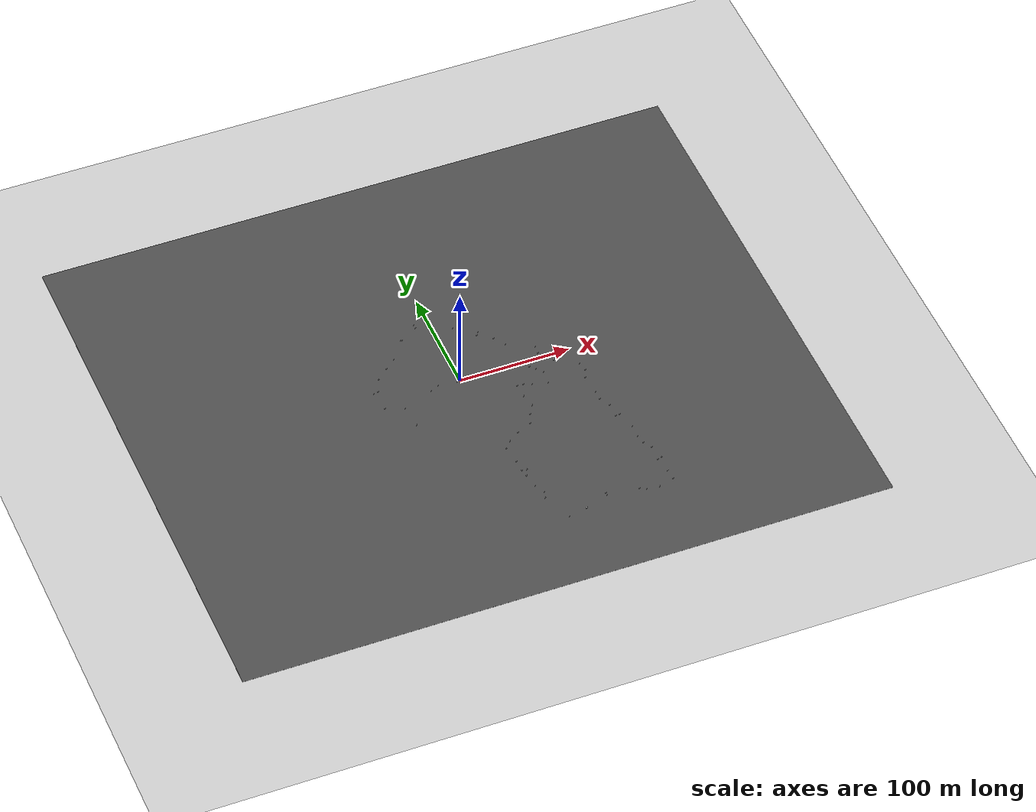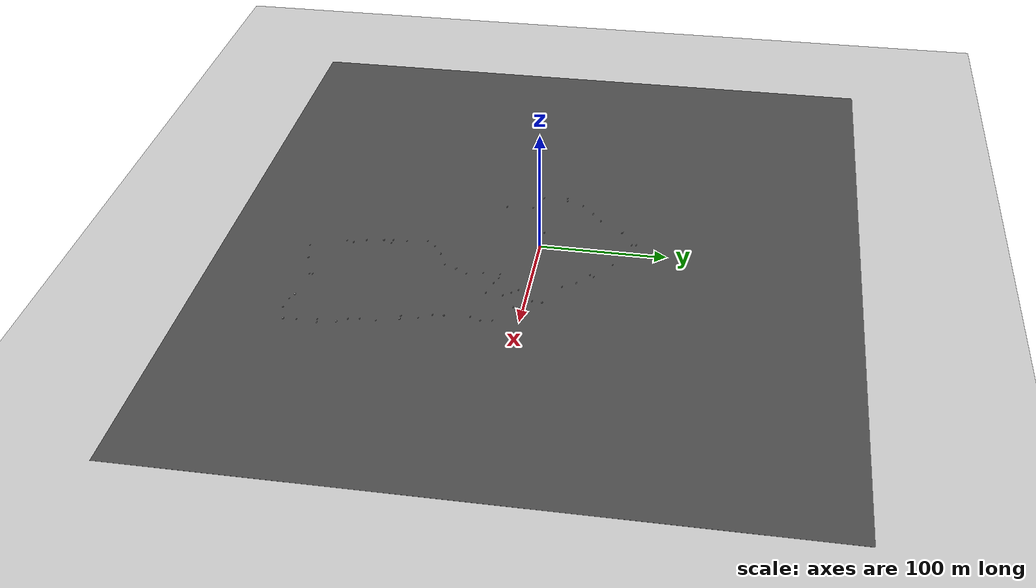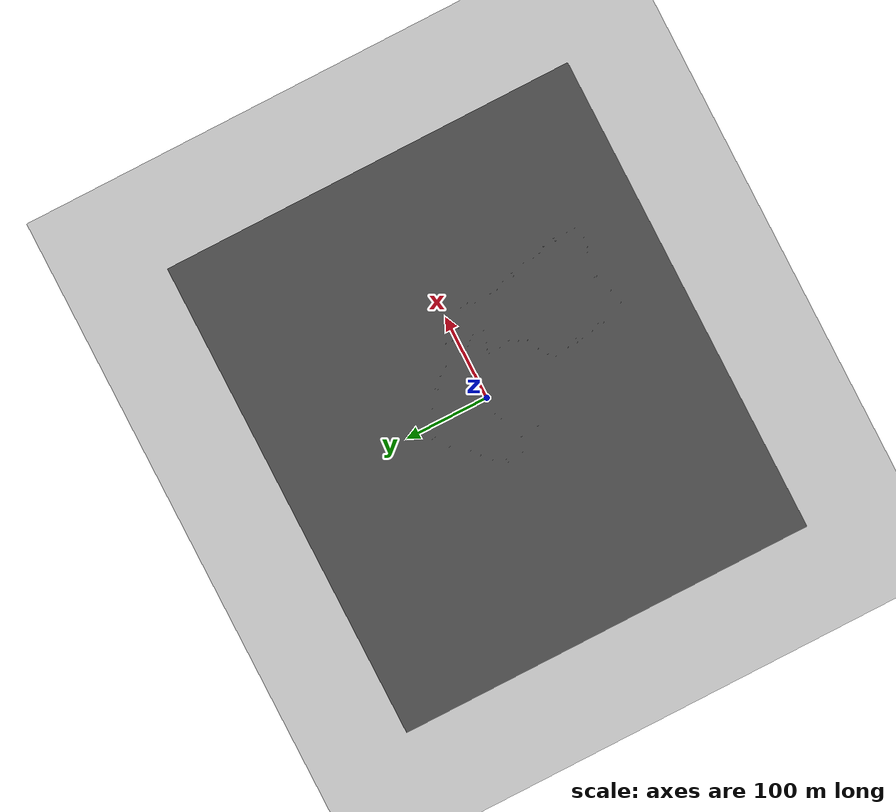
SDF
<sdf version="1.7">
 <world name="default">
  <light name="sun" type="directional">
   <pose>0 0 10 0 -0 0</pose>
   <diffuse>0.8 0.8 0.8 1</diffuse>
   <specular>0.2 0.2 0.2 1</specular>
   <attenuation>
    <range>1000</range>
    <constant>0.9</constant>
    <linear>0.01</linear>
    <quadratic>0.001</quadratic>
   </attenuation>
   <direction>-0.5 0.1 -0.9</direction>
   <spot><inner_angle>0</inner_angle><outer_angle>0</outer_angle><falloff>0</falloff></spot>
  </light>
  <model name="ground_plane">
   <static>1</static>
   <link name="link">
    <collision name="collision">
     <geometry><plane><normal>0 0 1</normal><size>100 100</size></plane></geometry>
     <surface><friction><ode><mu>100</mu><mu2>50</mu2></ode></friction></surface>
    </collision>
    <visual name="visual">
     <cast_shadows>0</cast_shadows>
     <geometry><plane><normal>0 0 1</normal><size>100 100</size></plane></geometry>
     <material>
      <script><uri>file://media/materials/scripts/gazebo.material</uri><name>Gazebo/Grey</name></script>
     </material>
    </visual>
   </link>
  </model>
  <gravity>0 0 -9.8</gravity>
  <magnetic_field>6e-06 2.3e-05 -4.2e-05</magnetic_field>
  <atmosphere type="adiabatic"/>
  <physics type="ode">
   <max_step_size>0.001</max_step_size>
   <real_time_factor>1</real_time_factor>
   <real_time_update_rate>1000</real_time_update_rate>
  </physics>
  <scene><ambient>0.4 0.4 0.4 1</ambient><background>0.7 0.7 0.7 1</background><shadows>1</shadows></scene>
  <audio><device>default</device></audio>
  <spherical_coordinates>
   <surface_model>EARTH_WGS84</surface_model>
   <latitude_deg>0</latitude_deg>
   <longitude_deg>0</longitude_deg>
   <elevation>0</elevation>
   <heading_deg>0</heading_deg>
  </spherical_coordinates>
  <model name="obstaculos">
   <link name="link_2">
    <inertial>
     <mass>1</mass>
     <inertia><ixx>0.145833</ixx><ixy>0</ixy><ixz>0</ixz><iyy>0.145833</iyy><iyz>0</iyz><izz>0.125</izz></inertia>
    </inertial>
    <pose>-68.8345 49.6018 0 0 -0 0</pose>
    <visual name="visual">
     <geometry><cylinder><radius>0.5</radius><length>1</length></cylinder></geometry>
     <material>
      <lighting>1</lighting>
      <script><uri>file://media/materials/scripts/gazebo.material</uri><name>Gazebo/Grey</name></script>
      <shader type="pixel"/>
     </material>
    </visual>
    <collision name="collision">
     <geometry><cylinder><radius>0.5</radius><length>1</length></cylinder></geometry>
     <surface>
      <friction>
       <ode><mu>1</mu><mu2>1</mu2><fdir1>0 0 0</fdir1><slip1>0</slip1><slip2>0</slip2></ode>
       <torsional>
        <coefficient>1</coefficient>
        <patch_radius>0</patch_radius>
        <surface_radius>0</surface_radius>
        <use_patch_radius>1</use_patch_radius>
        <ode><slip>0</slip></ode>
       </torsional>
      </friction>
      <bounce><restitution_coefficient>0</restitution_coefficient><threshold>1e+06</threshold></bounce>
      <contact>
       <collide_without_contact>0</collide_without_contact>
       <collide_without_contact_bitmask>1</collide_without_contact_bitmask>
       <collide_bitmask>1</collide_bitmask>
       <ode>
        <soft_cfm>0</soft_cfm>
        <soft_erp>0.2</soft_erp>
        <kp>1e+13</kp>
        <kd>1</kd>
        <max_vel>0.01</max_vel>
        <min_depth>0</min_depth>
       </ode>
       <bullet>
        <split_impulse>1</split_impulse>
        <split_impulse_penetration_threshold>-0.01</split_impulse_penetration_threshold>
        <soft_cfm>0</soft_cfm>
        <soft_erp>0.2</soft_erp>
        <kp>1e+13</kp>
        <kd>1</kd>
       </bullet>
      </contact>
     </surface>
    </collision>
   </link>
   <link name="link_10">
    <inertial>
     <mass>1</mass>
     <inertia><ixx>0.145833</ixx><ixy>0</ixy><ixz>0</ixz><iyy>0.145833</iyy><iyz>0</iyz><izz>0.125</izz></inertia>
    </inertial>
    <pose>23.917 41.4838 0 0 -0 0</pose>
    <visual name="visual">
     <geometry><cylinder><radius>0.5</radius><length>1</length></cylinder></geometry>
     <material>
      <lighting>1</lighting>
      <script><uri>file://media/materials/scripts/gazebo.material</uri><name>Gazebo/Grey</name></script>
      <shader type="pixel"/>
     </material>
    </visual>
    <collision name="collision">
     <geometry><cylinder><radius>0.5</radius><length>1</length></cylinder></geometry>
     <surface>
      <friction>
       <ode><mu>1</mu><mu2>1</mu2><fdir1>0 0 0</fdir1><slip1>0</slip1><slip2>0</slip2></ode>
       <torsional>
        <coefficient>1</coefficient>
        <patch_radius>0</patch_radius>
        <surface_radius>0</surface_radius>
        <use_patch_radius>1</use_patch_radius>
        <ode><slip>0</slip></ode>
       </torsional>
      </friction>
      <bounce><restitution_coefficient>0</restitution_coefficient><threshold>1e+06</threshold></bounce>
      <contact>
       <collide_without_contact>0</collide_without_contact>
       <collide_without_contact_bitmask>1</collide_without_contact_bitmask>
       <collide_bitmask>1</collide_bitmask>
       <ode>
        <soft_cfm>0</soft_cfm>
        <soft_erp>0.2</soft_erp>
        <kp>1e+13</kp>
        <kd>1</kd>
        <max_vel>0.01</max_vel>
        <min_depth>0</min_depth>
       </ode>
       <bullet>
        <split_impulse>1</split_impulse>
        <split_impulse_penetration_threshold>-0.01</split_impulse_penetration_threshold>
        <soft_cfm>0</soft_cfm>
        <soft_erp>0.2</soft_erp>
        <kp>1e+13</kp>
        <kd>1</kd>
       </bullet>
      </contact>
     </surface>
    </collision>
   </link>
   <link name="link_11">
    <inertial>
     <mass>1</mass>
     <inertia><ixx>0.145833</ixx><ixy>0</ixy><ixz>0</ixz><iyy>0.145833</iyy><iyz>0</iyz><izz>0.125</izz></inertia>
    </inertial>
    <pose>27.1261 22.4083 0 0 -0 0</pose>
    <visual name="visual">
     <geometry><cylinder><radius>0.5</radius><length>1</length></cylinder></geometry>
     <material>
      <lighting>1</lighting>
      <script><uri>file://media/materials/scripts/gazebo.material</uri><name>Gazebo/Grey</name></script>
      <shader type="pixel"/>
     </material>
    </visual>
    <collision name="collision">
     <geometry><cylinder><radius>0.5</radius><length>1</length></cylinder></geometry>
     <surface>
      <friction>
       <ode><mu>1</mu><mu2>1</mu2><fdir1>0 0 0</fdir1><slip1>0</slip1><slip2>0</slip2></ode>
       <torsional>
        <coefficient>1</coefficient>
        <patch_radius>0</patch_radius>
        <surface_radius>0</surface_radius>
        <use_patch_radius>1</use_patch_radius>
        <ode><slip>0</slip></ode>
       </torsional>
      </friction>
      <bounce><restitution_coefficient>0</restitution_coefficient><threshold>1e+06</threshold></bounce>
      <contact>
       <collide_without_contact>0</collide_without_contact>
       <collide_without_contact_bitmask>1</collide_without_contact_bitmask>
       <collide_bitmask>1</collide_bitmask>
       <ode>
        <soft_cfm>0</soft_cfm>
        <soft_erp>0.2</soft_erp>
        <kp>1e+13</kp>
        <kd>1</kd>
        <max_vel>0.01</max_vel>
        <min_depth>0</min_depth>
       </ode>
       <bullet>
        <split_impulse>1</split_impulse>
        <split_impulse_penetration_threshold>-0.01</split_impulse_penetration_threshold>
        <soft_cfm>0</soft_cfm>
        <soft_erp>0.2</soft_erp>
        <kp>1e+13</kp>
        <kd>1</kd>
       </bullet>
      </contact>
     </surface>
    </collision>
   </link>
   <link name="link_12">
    <inertial>
     <mass>1</mass>
     <inertia><ixx>0.145833</ixx><ixy>0</ixy><ixz>0</ixz><iyy>0.145833</iyy><iyz>0</iyz><izz>0.125</izz></inertia>
    </inertial>
    <pose>13.8228 25.9981 0 0 -0 0</pose>
    <visual name="visual">
     <geometry><cylinder><radius>0.5</radius><length>1</length></cylinder></geometry>
     <material>
      <lighting>1</lighting>
      <script><uri>file://media/materials/scripts/gazebo.material</uri><name>Gazebo/Grey</name></script>
      <shader type="pixel"/>
     </material>
    </visual>
    <collision name="collision">
     <geometry><cylinder><radius>0.5</radius><length>1</length></cylinder></geometry>
     <surface>
      <friction>
       <ode><mu>1</mu><mu2>1</mu2><fdir1>0 0 0</fdir1><slip1>0</slip1><slip2>0</slip2></ode>
       <torsional>
        <coefficient>1</coefficient>
        <patch_radius>0</patch_radius>
        <surface_radius>0</surface_radius>
        <use_patch_radius>1</use_patch_radius>
        <ode><slip>0</slip></ode>
       </torsional>
      </friction>
      <bounce><restitution_coefficient>0</restitution_coefficient><threshold>1e+06</threshold></bounce>
      <contact>
       <collide_without_contact>0</collide_without_contact>
       <collide_without_contact_bitmask>1</collide_without_contact_bitmask>
       <collide_bitmask>1</collide_bitmask>
       <ode>
        <soft_cfm>0</soft_cfm>
        <soft_erp>0.2</soft_erp>
        <kp>1e+13</kp>
        <kd>1</kd>
        <max_vel>0.01</max_vel>
        <min_depth>0</min_depth>
       </ode>
       <bullet>
        <split_impulse>1</split_impulse>
        <split_impulse_penetration_threshold>-0.01</split_impulse_penetration_threshold>
        <soft_cfm>0</soft_cfm>
        <soft_erp>0.2</soft_erp>
        <kp>1e+13</kp>
        <kd>1</kd>
       </bullet>
      </contact>
     </surface>
    </collision>
   </link>
   <link name="link_13">
    <inertial>
     <mass>1</mass>
     <inertia>
      <ixx>0.166667</ixx>
      <ixy>0</ixy>
      <ixz>0</ixz>
      <iyy>0.166667</iyy>
      <iyz>0</iyz>
      <izz>0.166667</izz>
     </inertia>
    </inertial>
    <pose>6.80401 28.6836 0 0 -0 0</pose>
    <visual name="visual">
     <geometry><box><size>1 1 1</size></box></geometry>
     <material>
      <lighting>1</lighting>
      <script><uri>file://media/materials/scripts/gazebo.material</uri><name>Gazebo/Grey</name></script>
      <shader type="pixel"/>
     </material>
    </visual>
    <collision name="collision">
     <geometry><box><size>1 1 1</size></box></geometry>
     <surface>
      <friction>
       <ode><mu>1</mu><mu2>1</mu2><fdir1>0 0 0</fdir1><slip1>0</slip1><slip2>0</slip2></ode>
       <torsional>
        <coefficient>1</coefficient>
        <patch_radius>0</patch_radius>
        <surface_radius>0</surface_radius>
        <use_patch_radius>1</use_patch_radius>
        <ode><slip>0</slip></ode>
       </torsional>
      </friction>
      <bounce><restitution_coefficient>0</restitution_coefficient><threshold>1e+06</threshold></bounce>
      <contact>
       <collide_without_contact>0</collide_without_contact>
       <collide_without_contact_bitmask>1</collide_without_contact_bitmask>
       <collide_bitmask>1</collide_bitmask>
       <ode>
        <soft_cfm>0</soft_cfm>
        <soft_erp>0.2</soft_erp>
        <kp>1e+13</kp>
        <kd>1</kd>
        <max_vel>0.01</max_vel>
        <min_depth>0</min_depth>
       </ode>
       <bullet>
        <split_impulse>1</split_impulse>
        <split_impulse_penetration_threshold>-0.01</split_impulse_penetration_threshold>
        <soft_cfm>0</soft_cfm>
        <soft_erp>0.2</soft_erp>
        <kp>1e+13</kp>
        <kd>1</kd>
       </bullet>
      </contact>
     </surface>
    </collision>
   </link>
   <link name="link_14">
    <inertial>
     <mass>1</mass>
     <inertia><ixx>0.145833</ixx><ixy>0</ixy><ixz>0</ixz><iyy>0.145833</iyy><iyz>0</iyz><izz>0.125</izz></inertia>
    </inertial>
    <pose>1.91987 15.5386 0 0 -0 0</pose>
    <visual name="visual">
     <geometry><cylinder><radius>0.5</radius><length>1</length></cylinder></geometry>
     <material>
      <lighting>1</lighting>
      <script><uri>file://media/materials/scripts/gazebo.material</uri><name>Gazebo/Grey</name></script>
      <shader type="pixel"/>
     </material>
    </visual>
    <collision name="collision">
     <geometry><cylinder><radius>0.5</radius><length>1</length></cylinder></geometry>
     <surface>
      <friction>
       <ode><mu>1</mu><mu2>1</mu2><fdir1>0 0 0</fdir1><slip1>0</slip1><slip2>0</slip2></ode>
       <torsional>
        <coefficient>1</coefficient>
        <patch_radius>0</patch_radius>
        <surface_radius>0</surface_radius>
        <use_patch_radius>1</use_patch_radius>
        <ode><slip>0</slip></ode>
       </torsional>
      </friction>
      <bounce><restitution_coefficient>0</restitution_coefficient><threshold>1e+06</threshold></bounce>
      <contact>
       <collide_without_contact>0</collide_without_contact>
       <collide_without_contact_bitmask>1</collide_without_contact_bitmask>
       <collide_bitmask>1</collide_bitmask>
       <ode>
        <soft_cfm>0</soft_cfm>
        <soft_erp>0.2</soft_erp>
        <kp>1e+13</kp>
        <kd>1</kd>
        <max_vel>0.01</max_vel>
        <min_depth>0</min_depth>
       </ode>
       <bullet>
        <split_impulse>1</split_impulse>
        <split_impulse_penetration_threshold>-0.01</split_impulse_penetration_threshold>
        <soft_cfm>0</soft_cfm>
        <soft_erp>0.2</soft_erp>
        <kp>1e+13</kp>
        <kd>1</kd>
       </bullet>
      </contact>
     </surface>
    </collision>
   </link>
   <link name="link_15">
    <inertial>
     <mass>1</mass>
     <inertia><ixx>0.145833</ixx><ixy>0</ixy><ixz>0</ixz><iyy>0.145833</iyy><iyz>0</iyz><izz>0.125</izz></inertia>
    </inertial>
    <pose>4.60069 2.83892 0 0 -0 0</pose>
    <visual name="visual">
     <geometry><cylinder><radius>0.5</radius><length>1</length></cylinder></geometry>
     <material>
      <lighting>1</lighting>
      <script><uri>file://media/materials/scripts/gazebo.material</uri><name>Gazebo/Grey</name></script>
      <shader type="pixel"/>
     </material>
    </visual>
    <collision name="collision">
     <geometry><cylinder><radius>0.5</radius><length>1</length></cylinder></geometry>
     <surface>
      <friction>
       <ode><mu>1</mu><mu2>1</mu2><fdir1>0 0 0</fdir1><slip1>0</slip1><slip2>0</slip2></ode>
       <torsional>
        <coefficient>1</coefficient>
        <patch_radius>0</patch_radius>
        <surface_radius>0</surface_radius>
        <use_patch_radius>1</use_patch_radius>
        <ode><slip>0</slip></ode>
       </torsional>
      </friction>
      <bounce><restitution_coefficient>0</restitution_coefficient><threshold>1e+06</threshold></bounce>
      <contact>
       <collide_without_contact>0</collide_without_contact>
       <collide_without_contact_bitmask>1</collide_without_contact_bitmask>
       <collide_bitmask>1</collide_bitmask>
       <ode>
        <soft_cfm>0</soft_cfm>
        <soft_erp>0.2</soft_erp>
        <kp>1e+13</kp>
        <kd>1</kd>
        <max_vel>0.01</max_vel>
        <min_depth>0</min_depth>
       </ode>
       <bullet>
        <split_impulse>1</split_impulse>
        <split_impulse_penetration_threshold>-0.01</split_impulse_penetration_threshold>
        <soft_cfm>0</soft_cfm>
        <soft_erp>0.2</soft_erp>
        <kp>1e+13</kp>
        <kd>1</kd>
       </bullet>
      </contact>
     </surface>
    </collision>
   </link>
   <link name="link_16">
    <inertial>
     <mass>1</mass>
     <inertia><ixx>0.145833</ixx><ixy>0</ixy><ixz>0</ixz><iyy>0.145833</iyy><iyz>0</iyz><izz>0.125</izz></inertia>
    </inertial>
    <pose>1.55298 28.6763 0 0 -0 0</pose>
    <visual name="visual">
     <geometry><cylinder><radius>0.5</radius><length>1</length></cylinder></geometry>
     <material>
      <lighting>1</lighting>
      <script><uri>file://media/materials/scripts/gazebo.material</uri><name>Gazebo/Grey</name></script>
      <shader type="pixel"/>
     </material>
    </visual>
    <collision name="collision">
     <geometry><cylinder><radius>0.5</radius><length>1</length></cylinder></geometry>
     <surface>
      <friction>
       <ode><mu>1</mu><mu2>1</mu2><fdir1>0 0 0</fdir1><slip1>0</slip1><slip2>0</slip2></ode>
       <torsional>
        <coefficient>1</coefficient>
        <patch_radius>0</patch_radius>
        <surface_radius>0</surface_radius>
        <use_patch_radius>1</use_patch_radius>
        <ode><slip>0</slip></ode>
       </torsional>
      </friction>
      <bounce><restitution_coefficient>0</restitution_coefficient><threshold>1e+06</threshold></bounce>
      <contact>
       <collide_without_contact>0</collide_without_contact>
       <collide_without_contact_bitmask>1</collide_without_contact_bitmask>
       <collide_bitmask>1</collide_bitmask>
       <ode>
        <soft_cfm>0</soft_cfm>
        <soft_erp>0.2</soft_erp>
        <kp>1e+13</kp>
        <kd>1</kd>
        <max_vel>0.01</max_vel>
        <min_depth>0</min_depth>
       </ode>
       <bullet>
        <split_impulse>1</split_impulse>
        <split_impulse_penetration_threshold>-0.01</split_impulse_penetration_threshold>
        <soft_cfm>0</soft_cfm>
        <soft_erp>0.2</soft_erp>
        <kp>1e+13</kp>
        <kd>1</kd>
       </bullet>
      </contact>
     </surface>
    </collision>
   </link>
   <link name="link_17">
    <inertial>
     <mass>1</mass>
     <inertia><ixx>0.145833</ixx><ixy>0</ixy><ixz>0</ixz><iyy>0.145833</iyy><iyz>0</iyz><izz>0.125</izz></inertia>
    </inertial>
    <pose>-4.79054 -16.0996 0 0 -0 0</pose>
    <visual name="visual">
     <geometry><cylinder><radius>0.5</radius><length>1</length></cylinder></geometry>
     <material>
      <lighting>1</lighting>
      <script><uri>file://media/materials/scripts/gazebo.material</uri><name>Gazebo/Grey</name></script>
      <shader type="pixel"/>
     </material>
    </visual>
    <collision name="collision">
     <geometry><cylinder><radius>0.5</radius><length>1</length></cylinder></geometry>
     <surface>
      <friction>
       <ode><mu>1</mu><mu2>1</mu2><fdir1>0 0 0</fdir1><slip1>0</slip1><slip2>0</slip2></ode>
       <torsional>
        <coefficient>1</coefficient>
        <patch_radius>0</patch_radius>
        <surface_radius>0</surface_radius>
        <use_patch_radius>1</use_patch_radius>
        <ode><slip>0</slip></ode>
       </torsional>
      </friction>
      <bounce><restitution_coefficient>0</restitution_coefficient><threshold>1e+06</threshold></bounce>
      <contact>
       <collide_without_contact>0</collide_without_contact>
       <collide_without_contact_bitmask>1</collide_without_contact_bitmask>
       <collide_bitmask>1</collide_bitmask>
       <ode>
        <soft_cfm>0</soft_cfm>
        <soft_erp>0.2</soft_erp>
        <kp>1e+13</kp>
        <kd>1</kd>
        <max_vel>0.01</max_vel>
        <min_depth>0</min_depth>
       </ode>
       <bullet>
        <split_impulse>1</split_impulse>
        <split_impulse_penetration_threshold>-0.01</split_impulse_penetration_threshold>
        <soft_cfm>0</soft_cfm>
        <soft_erp>0.2</soft_erp>
        <kp>1e+13</kp>
        <kd>1</kd>
       </bullet>
      </contact>
     </surface>
    </collision>
   </link>
   <link name="link_18">
    <inertial>
     <mass>1</mass>
     <inertia>
      <ixx>0.166667</ixx>
      <ixy>0</ixy>
      <ixz>0</ixz>
      <iyy>0.166667</iyy>
      <iyz>0</iyz>
      <izz>0.166667</izz>
     </inertia>
    </inertial>
    <pose>-0.666415 -6.12016 0 0 -0 0</pose>
    <visual name="visual">
     <geometry><box><size>1 1 1</size></box></geometry>
     <material>
      <lighting>1</lighting>
      <script><uri>file://media/materials/scripts/gazebo.material</uri><name>Gazebo/Grey</name></script>
      <shader type="pixel"/>
     </material>
    </visual>
    <collision name="collision">
     <geometry><box><size>1 1 1</size></box></geometry>
     <surface>
      <friction>
       <ode><mu>1</mu><mu2>1</mu2><fdir1>0 0 0</fdir1><slip1>0</slip1><slip2>0</slip2></ode>
       <torsional>
        <coefficient>1</coefficient>
        <patch_radius>0</patch_radius>
        <surface_radius>0</surface_radius>
        <use_patch_radius>1</use_patch_radius>
        <ode><slip>0</slip></ode>
       </torsional>
      </friction>
      <bounce><restitution_coefficient>0</restitution_coefficient><threshold>1e+06</threshold></bounce>
      <contact>
       <collide_without_contact>0</collide_without_contact>
       <collide_without_contact_bitmask>1</collide_without_contact_bitmask>
       <collide_bitmask>1</collide_bitmask>
       <ode>
        <soft_cfm>0</soft_cfm>
        <soft_erp>0.2</soft_erp>
        <kp>1e+13</kp>
        <kd>1</kd>
        <max_vel>0.01</max_vel>
        <min_depth>0</min_depth>
       </ode>
       <bullet>
        <split_impulse>1</split_impulse>
        <split_impulse_penetration_threshold>-0.01</split_impulse_penetration_threshold>
        <soft_cfm>0</soft_cfm>
        <soft_erp>0.2</soft_erp>
        <kp>1e+13</kp>
        <kd>1</kd>
       </bullet>
      </contact>
     </surface>
    </collision>
   </link>
   <link name="link_19">
    <inertial>
     <mass>1</mass>
     <inertia><ixx>0.145833</ixx><ixy>0</ixy><ixz>0</ixz><iyy>0.145833</iyy><iyz>0</iyz><izz>0.125</izz></inertia>
    </inertial>
    <pose>-18.5164 -22.2528 0 0 -0 0</pose>
    <visual name="visual">
     <geometry><cylinder><radius>0.5</radius><length>1</length></cylinder></geometry>
     <material>
      <lighting>1</lighting>
      <script><uri>file://media/materials/scripts/gazebo.material</uri><name>Gazebo/Grey</name></script>
      <shader type="pixel"/>
     </material>
    </visual>
    <collision name="collision">
     <geometry><cylinder><radius>0.5</radius><length>1</length></cylinder></geometry>
     <surface>
      <friction>
       <ode><mu>1</mu><mu2>1</mu2><fdir1>0 0 0</fdir1><slip1>0</slip1><slip2>0</slip2></ode>
       <torsional>
        <coefficient>1</coefficient>
        <patch_radius>0</patch_radius>
        <surface_radius>0</surface_radius>
        <use_patch_radius>1</use_patch_radius>
        <ode><slip>0</slip></ode>
       </torsional>
      </friction>
      <bounce><restitution_coefficient>0</restitution_coefficient><threshold>1e+06</threshold></bounce>
      <contact>
       <collide_without_contact>0</collide_without_contact>
       <collide_without_contact_bitmask>1</collide_without_contact_bitmask>
       <collide_bitmask>1</collide_bitmask>
       <ode>
        <soft_cfm>0</soft_cfm>
        <soft_erp>0.2</soft_erp>
        <kp>1e+13</kp>
        <kd>1</kd>
        <max_vel>0.01</max_vel>
        <min_depth>0</min_depth>
       </ode>
       <bullet>
        <split_impulse>1</split_impulse>
        <split_impulse_penetration_threshold>-0.01</split_impulse_penetration_threshold>
        <soft_cfm>0</soft_cfm>
        <soft_erp>0.2</soft_erp>
        <kp>1e+13</kp>
        <kd>1</kd>
       </bullet>
      </contact>
     </surface>
    </collision>
   </link>
   <link name="link_20">
    <inertial>
     <mass>1</mass>
     <inertia><ixx>0.145833</ixx><ixy>0</ixy><ixz>0</ixz><iyy>0.145833</iyy><iyz>0</iyz><izz>0.125</izz></inertia>
    </inertial>
    <pose>-28.5098 -28.9625 0 0 -0 0</pose>
    <visual name="visual">
     <geometry><cylinder><radius>0.5</radius><length>1</length></cylinder></geometry>
     <material>
      <lighting>1</lighting>
      <script><uri>file://media/materials/scripts/gazebo.material</uri><name>Gazebo/Grey</name></script>
      <shader type="pixel"/>
     </material>
    </visual>
    <collision name="collision">
     <geometry><cylinder><radius>0.5</radius><length>1</length></cylinder></geometry>
     <surface>
      <friction>
       <ode><mu>1</mu><mu2>1</mu2><fdir1>0 0 0</fdir1><slip1>0</slip1><slip2>0</slip2></ode>
       <torsional>
        <coefficient>1</coefficient>
        <patch_radius>0</patch_radius>
        <surface_radius>0</surface_radius>
        <use_patch_radius>1</use_patch_radius>
        <ode><slip>0</slip></ode>
       </torsional>
      </friction>
      <bounce><restitution_coefficient>0</restitution_coefficient><threshold>1e+06</threshold></bounce>
      <contact>
       <collide_without_contact>0</collide_without_contact>
       <collide_without_contact_bitmask>1</collide_without_contact_bitmask>
       <collide_bitmask>1</collide_bitmask>
       <ode>
        <soft_cfm>0</soft_cfm>
        <soft_erp>0.2</soft_erp>
        <kp>1e+13</kp>
        <kd>1</kd>
        <max_vel>0.01</max_vel>
        <min_depth>0</min_depth>
       </ode>
       <bullet>
        <split_impulse>1</split_impulse>
        <split_impulse_penetration_threshold>-0.01</split_impulse_penetration_threshold>
        <soft_cfm>0</soft_cfm>
        <soft_erp>0.2</soft_erp>
        <kp>1e+13</kp>
        <kd>1</kd>
       </bullet>
      </contact>
     </surface>
    </collision>
   </link>
   <link name="link_21">
    <inertial>
     <mass>1</mass>
     <inertia><ixx>0.145833</ixx><ixy>0</ixy><ixz>0</ixz><iyy>0.145833</iyy><iyz>0</iyz><izz>0.125</izz></inertia>
    </inertial>
    <pose>-34.6644 -35.9676 0 0 -0 0</pose>
    <visual name="visual">
     <geometry><cylinder><radius>0.5</radius><length>1</length></cylinder></geometry>
     <material>
      <lighting>1</lighting>
      <script><uri>file://media/materials/scripts/gazebo.material</uri><name>Gazebo/Grey</name></script>
      <shader type="pixel"/>
     </material>
    </visual>
    <collision name="collision">
     <geometry><cylinder><radius>0.5</radius><length>1</length></cylinder></geometry>
     <surface>
      <friction>
       <ode><mu>1</mu><mu2>1</mu2><fdir1>0 0 0</fdir1><slip1>0</slip1><slip2>0</slip2></ode>
       <torsional>
        <coefficient>1</coefficient>
        <patch_radius>0</patch_radius>
        <surface_radius>0</surface_radius>
        <use_patch_radius>1</use_patch_radius>
        <ode><slip>0</slip></ode>
       </torsional>
      </friction>
      <bounce><restitution_coefficient>0</restitution_coefficient><threshold>1e+06</threshold></bounce>
      <contact>
       <collide_without_contact>0</collide_without_contact>
       <collide_without_contact_bitmask>1</collide_without_contact_bitmask>
       <collide_bitmask>1</collide_bitmask>
       <ode>
        <soft_cfm>0</soft_cfm>
        <soft_erp>0.2</soft_erp>
        <kp>1e+13</kp>
        <kd>1</kd>
        <max_vel>0.01</max_vel>
        <min_depth>0</min_depth>
       </ode>
       <bullet>
        <split_impulse>1</split_impulse>
        <split_impulse_penetration_threshold>-0.01</split_impulse_penetration_threshold>
        <soft_cfm>0</soft_cfm>
        <soft_erp>0.2</soft_erp>
        <kp>1e+13</kp>
        <kd>1</kd>
       </bullet>
      </contact>
     </surface>
    </collision>
   </link>
   <link name="link_22">
    <inertial>
     <mass>1</mass>
     <inertia><ixx>0.145833</ixx><ixy>0</ixy><ixz>0</ixz><iyy>0.145833</iyy><iyz>0</iyz><izz>0.125</izz></inertia>
    </inertial>
    <pose>-32.1922 -52.4288 0 0 -0 0</pose>
    <visual name="visual">
     <geometry><cylinder><radius>0.5</radius><length>1</length></cylinder></geometry>
     <material>
      <lighting>1</lighting>
      <script><uri>file://media/materials/scripts/gazebo.material</uri><name>Gazebo/Grey</name></script>
      <shader type="pixel"/>
     </material>
    </visual>
    <collision name="collision">
     <geometry><cylinder><radius>0.5</radius><length>1</length></cylinder></geometry>
     <surface>
      <friction>
       <ode><mu>1</mu><mu2>1</mu2><fdir1>0 0 0</fdir1><slip1>0</slip1><slip2>0</slip2></ode>
       <torsional>
        <coefficient>1</coefficient>
        <patch_radius>0</patch_radius>
        <surface_radius>0</surface_radius>
        <use_patch_radius>1</use_patch_radius>
        <ode><slip>0</slip></ode>
       </torsional>
      </friction>
      <bounce><restitution_coefficient>0</restitution_coefficient><threshold>1e+06</threshold></bounce>
      <contact>
       <collide_without_contact>0</collide_without_contact>
       <collide_without_contact_bitmask>1</collide_without_contact_bitmask>
       <collide_bitmask>1</collide_bitmask>
       <ode>
        <soft_cfm>0</soft_cfm>
        <soft_erp>0.2</soft_erp>
        <kp>1e+13</kp>
        <kd>1</kd>
        <max_vel>0.01</max_vel>
        <min_depth>0</min_depth>
       </ode>
       <bullet>
        <split_impulse>1</split_impulse>
        <split_impulse_penetration_threshold>-0.01</split_impulse_penetration_threshold>
        <soft_cfm>0</soft_cfm>
        <soft_erp>0.2</soft_erp>
        <kp>1e+13</kp>
        <kd>1</kd>
       </bullet>
      </contact>
     </surface>
    </collision>
   </link>
   <link name="link_23">
    <inertial>
     <mass>1</mass>
     <inertia>
      <ixx>0.166667</ixx>
      <ixy>0</ixy>
      <ixz>0</ixz>
      <iyy>0.166667</iyy>
      <iyz>0</iyz>
      <izz>0.166667</izz>
     </inertia>
    </inertial>
    <pose>-27.5481 -64.2829 0 0 -0 0</pose>
    <visual name="visual">
     <geometry><box><size>1 1 1</size></box></geometry>
     <material>
      <lighting>1</lighting>
      <script><uri>file://media/materials/scripts/gazebo.material</uri><name>Gazebo/Grey</name></script>
      <shader type="pixel"/>
     </material>
    </visual>
    <collision name="collision">
     <geometry><box><size>1 1 1</size></box></geometry>
     <surface>
      <friction>
       <ode><mu>1</mu><mu2>1</mu2><fdir1>0 0 0</fdir1><slip1>0</slip1><slip2>0</slip2></ode>
       <torsional>
        <coefficient>1</coefficient>
        <patch_radius>0</patch_radius>
        <surface_radius>0</surface_radius>
        <use_patch_radius>1</use_patch_radius>
        <ode><slip>0</slip></ode>
       </torsional>
      </friction>
      <bounce><restitution_coefficient>0</restitution_coefficient><threshold>1e+06</threshold></bounce>
      <contact>
       <collide_without_contact>0</collide_without_contact>
       <collide_without_contact_bitmask>1</collide_without_contact_bitmask>
       <collide_bitmask>1</collide_bitmask>
       <ode>
        <soft_cfm>0</soft_cfm>
        <soft_erp>0.2</soft_erp>
        <kp>1e+13</kp>
        <kd>1</kd>
        <max_vel>0.01</max_vel>
        <min_depth>0</min_depth>
       </ode>
       <bullet>
        <split_impulse>1</split_impulse>
        <split_impulse_penetration_threshold>-0.01</split_impulse_penetration_threshold>
        <soft_cfm>0</soft_cfm>
        <soft_erp>0.2</soft_erp>
        <kp>1e+13</kp>
        <kd>1</kd>
       </bullet>
      </contact>
     </surface>
    </collision>
   </link>
   <link name="link_24">
    <inertial>
     <mass>1</mass>
     <inertia>
      <ixx>0.166667</ixx>
      <ixy>0</ixy>
      <ixz>0</ixz>
      <iyy>0.166667</iyy>
      <iyz>0</iyz>
      <izz>0.166667</izz>
     </inertia>
    </inertial>
    <pose>-30.5685 -70.8884 0 0 -0 0</pose>
    <visual name="visual">
     <geometry><box><size>1 1 1</size></box></geometry>
     <material>
      <lighting>1</lighting>
      <script><uri>file://media/materials/scripts/gazebo.material</uri><name>Gazebo/Grey</name></script>
      <shader type="pixel"/>
     </material>
    </visual>
    <collision name="collision">
     <geometry><box><size>1 1 1</size></box></geometry>
     <surface>
      <friction>
       <ode><mu>1</mu><mu2>1</mu2><fdir1>0 0 0</fdir1><slip1>0</slip1><slip2>0</slip2></ode>
       <torsional>
        <coefficient>1</coefficient>
        <patch_radius>0</patch_radius>
        <surface_radius>0</surface_radius>
        <use_patch_radius>1</use_patch_radius>
        <ode><slip>0</slip></ode>
       </torsional>
      </friction>
      <bounce><restitution_coefficient>0</restitution_coefficient><threshold>1e+06</threshold></bounce>
      <contact>
       <collide_without_contact>0</collide_without_contact>
       <collide_without_contact_bitmask>1</collide_without_contact_bitmask>
       <collide_bitmask>1</collide_bitmask>
       <ode>
        <soft_cfm>0</soft_cfm>
        <soft_erp>0.2</soft_erp>
        <kp>1e+13</kp>
        <kd>1</kd>
        <max_vel>0.01</max_vel>
        <min_depth>0</min_depth>
       </ode>
       <bullet>
        <split_impulse>1</split_impulse>
        <split_impulse_penetration_threshold>-0.01</split_impulse_penetration_threshold>
        <soft_cfm>0</soft_cfm>
        <soft_erp>0.2</soft_erp>
        <kp>1e+13</kp>
        <kd>1</kd>
       </bullet>
      </contact>
     </surface>
    </collision>
   </link>
   <link name="link_25">
    <inertial>
     <mass>1</mass>
     <inertia><ixx>0.145833</ixx><ixy>0</ixy><ixz>0</ixz><iyy>0.145833</iyy><iyz>0</iyz><izz>0.125</izz></inertia>
    </inertial>
    <pose>-31.8533 -63.6673 0 0 -0 0</pose>
    <visual name="visual">
     <geometry><cylinder><radius>0.5</radius><length>1</length></cylinder></geometry>
     <material>
      <lighting>1</lighting>
      <script><uri>file://media/materials/scripts/gazebo.material</uri><name>Gazebo/Grey</name></script>
      <shader type="pixel"/>
     </material>
    </visual>
    <collision name="collision">
     <geometry><cylinder><radius>0.5</radius><length>1</length></cylinder></geometry>
     <surface>
      <friction>
       <ode><mu>1</mu><mu2>1</mu2><fdir1>0 0 0</fdir1><slip1>0</slip1><slip2>0</slip2></ode>
       <torsional>
        <coefficient>1</coefficient>
        <patch_radius>0</patch_radius>
        <surface_radius>0</surface_radius>
        <use_patch_radius>1</use_patch_radius>
        <ode><slip>0</slip></ode>
       </torsional>
      </friction>
      <bounce><restitution_coefficient>0</restitution_coefficient><threshold>1e+06</threshold></bounce>
      <contact>
       <collide_without_contact>0</collide_without_contact>
       <collide_without_contact_bitmask>1</collide_without_contact_bitmask>
       <collide_bitmask>1</collide_bitmask>
       <ode>
        <soft_cfm>0</soft_cfm>
        <soft_erp>0.2</soft_erp>
        <kp>1e+13</kp>
        <kd>1</kd>
        <max_vel>0.01</max_vel>
        <min_depth>0</min_depth>
       </ode>
       <bullet>
        <split_impulse>1</split_impulse>
        <split_impulse_penetration_threshold>-0.01</split_impulse_penetration_threshold>
        <soft_cfm>0</soft_cfm>
        <soft_erp>0.2</soft_erp>
        <kp>1e+13</kp>
        <kd>1</kd>
       </bullet>
      </contact>
     </surface>
    </collision>
   </link>
   <link name="link_26">
    <inertial>
     <mass>1</mass>
     <inertia><ixx>0.145833</ixx><ixy>0</ixy><ixz>0</ixz><iyy>0.145833</iyy><iyz>0</iyz><izz>0.125</izz></inertia>
    </inertial>
    <pose>-28.4551 -84.4776 0 0 -0 0</pose>
    <visual name="visual">
     <geometry><cylinder><radius>0.5</radius><length>1</length></cylinder></geometry>
     <material>
      <lighting>1</lighting>
      <script><uri>file://media/materials/scripts/gazebo.material</uri><name>Gazebo/Grey</name></script>
      <shader type="pixel"/>
     </material>
    </visual>
    <collision name="collision">
     <geometry><cylinder><radius>0.5</radius><length>1</length></cylinder></geometry>
     <surface>
      <friction>
       <ode><mu>1</mu><mu2>1</mu2><fdir1>0 0 0</fdir1><slip1>0</slip1><slip2>0</slip2></ode>
       <torsional>
        <coefficient>1</coefficient>
        <patch_radius>0</patch_radius>
        <surface_radius>0</surface_radius>
        <use_patch_radius>1</use_patch_radius>
        <ode><slip>0</slip></ode>
       </torsional>
      </friction>
      <bounce><restitution_coefficient>0</restitution_coefficient><threshold>1e+06</threshold></bounce>
      <contact>
       <collide_without_contact>0</collide_without_contact>
       <collide_without_contact_bitmask>1</collide_without_contact_bitmask>
       <collide_bitmask>1</collide_bitmask>
       <ode>
        <soft_cfm>0</soft_cfm>
        <soft_erp>0.2</soft_erp>
        <kp>1e+13</kp>
        <kd>1</kd>
        <max_vel>0.01</max_vel>
        <min_depth>0</min_depth>
       </ode>
       <bullet>
        <split_impulse>1</split_impulse>
        <split_impulse_penetration_threshold>-0.01</split_impulse_penetration_threshold>
        <soft_cfm>0</soft_cfm>
        <soft_erp>0.2</soft_erp>
        <kp>1e+13</kp>
        <kd>1</kd>
       </bullet>
      </contact>
     </surface>
    </collision>
   </link>
   <link name="link_27">
    <inertial>
     <mass>1</mass>
     <inertia><ixx>0.145833</ixx><ixy>0</ixy><ixz>0</ixz><iyy>0.145833</iyy><iyz>0</iyz><izz>0.125</izz></inertia>
    </inertial>
    <pose>-23.9145 -93.9423 0 0 -0 0</pose>
    <visual name="visual">
     <geometry><cylinder><radius>0.5</radius><length>1</length></cylinder></geometry>
     <material>
      <lighting>1</lighting>
      <script><uri>file://media/materials/scripts/gazebo.material</uri><name>Gazebo/Grey</name></script>
      <shader type="pixel"/>
     </material>
    </visual>
    <collision name="collision">
     <geometry><cylinder><radius>0.5</radius><length>1</length></cylinder></geometry>
     <surface>
      <friction>
       <ode><mu>1</mu><mu2>1</mu2><fdir1>0 0 0</fdir1><slip1>0</slip1><slip2>0</slip2></ode>
       <torsional>
        <coefficient>1</coefficient>
        <patch_radius>0</patch_radius>
        <surface_radius>0</surface_radius>
        <use_patch_radius>1</use_patch_radius>
        <ode><slip>0</slip></ode>
       </torsional>
      </friction>
      <bounce><restitution_coefficient>0</restitution_coefficient><threshold>1e+06</threshold></bounce>
      <contact>
       <collide_without_contact>0</collide_without_contact>
       <collide_without_contact_bitmask>1</collide_without_contact_bitmask>
       <collide_bitmask>1</collide_bitmask>
       <ode>
        <soft_cfm>0</soft_cfm>
        <soft_erp>0.2</soft_erp>
        <kp>1e+13</kp>
        <kd>1</kd>
        <max_vel>0.01</max_vel>
        <min_depth>0</min_depth>
       </ode>
       <bullet>
        <split_impulse>1</split_impulse>
        <split_impulse_penetration_threshold>-0.01</split_impulse_penetration_threshold>
        <soft_cfm>0</soft_cfm>
        <soft_erp>0.2</soft_erp>
        <kp>1e+13</kp>
        <kd>1</kd>
       </bullet>
      </contact>
     </surface>
    </collision>
   </link>
   <link name="link_28">
    <inertial>
     <mass>1</mass>
     <inertia>
      <ixx>0.166667</ixx>
      <ixy>0</ixy>
      <ixz>0</ixz>
      <iyy>0.166667</iyy>
      <iyz>0</iyz>
      <izz>0.166667</izz>
     </inertia>
    </inertial>
    <pose>-25.5345 -99.8334 0 0 -0 0</pose>
    <visual name="visual">
     <geometry><box><size>1 1 1</size></box></geometry>
     <material>
      <lighting>1</lighting>
      <script><uri>file://media/materials/scripts/gazebo.material</uri><name>Gazebo/Grey</name></script>
      <shader type="pixel"/>
     </material>
    </visual>
    <collision name="collision">
     <geometry><box><size>1 1 1</size></box></geometry>
     <surface>
      <friction>
       <ode><mu>1</mu><mu2>1</mu2><fdir1>0 0 0</fdir1><slip1>0</slip1><slip2>0</slip2></ode>
       <torsional>
        <coefficient>1</coefficient>
        <patch_radius>0</patch_radius>
        <surface_radius>0</surface_radius>
        <use_patch_radius>1</use_patch_radius>
        <ode><slip>0</slip></ode>
       </torsional>
      </friction>
      <bounce><restitution_coefficient>0</restitution_coefficient><threshold>1e+06</threshold></bounce>
      <contact>
       <collide_without_contact>0</collide_without_contact>
       <collide_without_contact_bitmask>1</collide_without_contact_bitmask>
       <collide_bitmask>1</collide_bitmask>
       <ode>
        <soft_cfm>0</soft_cfm>
        <soft_erp>0.2</soft_erp>
        <kp>1e+13</kp>
        <kd>1</kd>
        <max_vel>0.01</max_vel>
        <min_depth>0</min_depth>
       </ode>
       <bullet>
        <split_impulse>1</split_impulse>
        <split_impulse_penetration_threshold>-0.01</split_impulse_penetration_threshold>
        <soft_cfm>0</soft_cfm>
        <soft_erp>0.2</soft_erp>
        <kp>1e+13</kp>
        <kd>1</kd>
       </bullet>
      </contact>
     </surface>
    </collision>
   </link>
   <link name="link_29">
    <inertial>
     <mass>1</mass>
     <inertia><ixx>0.145833</ixx><ixy>0</ixy><ixz>0</ixz><iyy>0.145833</iyy><iyz>0</iyz><izz>0.125</izz></inertia>
    </inertial>
    <pose>-14.7365 -126.863 0 0 -0 0</pose>
    <visual name="visual">
     <geometry><cylinder><radius>0.5</radius><length>1</length></cylinder></geometry>
     <material>
      <lighting>1</lighting>
      <script><uri>file://media/materials/scripts/gazebo.material</uri><name>Gazebo/Grey</name></script>
      <shader type="pixel"/>
     </material>
    </visual>
    <collision name="collision">
     <geometry><cylinder><radius>0.5</radius><length>1</length></cylinder></geometry>
     <surface>
      <friction>
       <ode><mu>1</mu><mu2>1</mu2><fdir1>0 0 0</fdir1><slip1>0</slip1><slip2>0</slip2></ode>
       <torsional>
        <coefficient>1</coefficient>
        <patch_radius>0</patch_radius>
        <surface_radius>0</surface_radius>
        <use_patch_radius>1</use_patch_radius>
        <ode><slip>0</slip></ode>
       </torsional>
      </friction>
      <bounce><restitution_coefficient>0</restitution_coefficient><threshold>1e+06</threshold></bounce>
      <contact>
       <collide_without_contact>0</collide_without_contact>
       <collide_without_contact_bitmask>1</collide_without_contact_bitmask>
       <collide_bitmask>1</collide_bitmask>
       <ode>
        <soft_cfm>0</soft_cfm>
        <soft_erp>0.2</soft_erp>
        <kp>1e+13</kp>
        <kd>1</kd>
        <max_vel>0.01</max_vel>
        <min_depth>0</min_depth>
       </ode>
       <bullet>
        <split_impulse>1</split_impulse>
        <split_impulse_penetration_threshold>-0.01</split_impulse_penetration_threshold>
        <soft_cfm>0</soft_cfm>
        <soft_erp>0.2</soft_erp>
        <kp>1e+13</kp>
        <kd>1</kd>
       </bullet>
      </contact>
     </surface>
    </collision>
   </link>
   <link name="link_3">
    <inertial>
     <mass>1</mass>
     <inertia><ixx>0.145833</ixx><ixy>0</ixy><ixz>0</ixz><iyy>0.145833</iyy><iyz>0</iyz><izz>0.125</izz></inertia>
    </inertial>
    <pose>-60.8834 53.5123 0 0 -0 0</pose>
    <visual name="visual">
     <geometry><cylinder><radius>0.5</radius><length>1</length></cylinder></geometry>
     <material>
      <lighting>1</lighting>
      <script><uri>file://media/materials/scripts/gazebo.material</uri><name>Gazebo/Grey</name></script>
      <shader type="pixel"/>
     </material>
    </visual>
    <collision name="collision">
     <geometry><cylinder><radius>0.5</radius><length>1</length></cylinder></geometry>
     <surface>
      <friction>
       <ode><mu>1</mu><mu2>1</mu2><fdir1>0 0 0</fdir1><slip1>0</slip1><slip2>0</slip2></ode>
       <torsional>
        <coefficient>1</coefficient>
        <patch_radius>0</patch_radius>
        <surface_radius>0</surface_radius>
        <use_patch_radius>1</use_patch_radius>
        <ode><slip>0</slip></ode>
       </torsional>
      </friction>
      <bounce><restitution_coefficient>0</restitution_coefficient><threshold>1e+06</threshold></bounce>
      <contact>
       <collide_without_contact>0</collide_without_contact>
       <collide_without_contact_bitmask>1</collide_without_contact_bitmask>
       <collide_bitmask>1</collide_bitmask>
       <ode>
        <soft_cfm>0</soft_cfm>
        <soft_erp>0.2</soft_erp>
        <kp>1e+13</kp>
        <kd>1</kd>
        <max_vel>0.01</max_vel>
        <min_depth>0</min_depth>
       </ode>
       <bullet>
        <split_impulse>1</split_impulse>
        <split_impulse_penetration_threshold>-0.01</split_impulse_penetration_threshold>
        <soft_cfm>0</soft_cfm>
        <soft_erp>0.2</soft_erp>
        <kp>1e+13</kp>
        <kd>1</kd>
       </bullet>
      </contact>
     </surface>
    </collision>
   </link>
   <link name="link_30">
    <inertial>
     <mass>1</mass>
     <inertia>
      <ixx>0.166667</ixx>
      <ixy>0</ixy>
      <ixz>0</ixz>
      <iyy>0.166667</iyy>
      <iyz>0</iyz>
      <izz>0.166667</izz>
     </inertia>
    </inertial>
    <pose>2.2833 -123.289 0 0 -0 0</pose>
    <visual name="visual">
     <geometry><box><size>1 1 1</size></box></geometry>
     <material>
      <lighting>1</lighting>
      <script><uri>file://media/materials/scripts/gazebo.material</uri><name>Gazebo/Grey</name></script>
      <shader type="pixel"/>
     </material>
    </visual>
    <collision name="collision">
     <geometry><box><size>1 1 1</size></box></geometry>
     <surface>
      <friction>
       <ode><mu>1</mu><mu2>1</mu2><fdir1>0 0 0</fdir1><slip1>0</slip1><slip2>0</slip2></ode>
       <torsional>
        <coefficient>1</coefficient>
        <patch_radius>0</patch_radius>
        <surface_radius>0</surface_radius>
        <use_patch_radius>1</use_patch_radius>
        <ode><slip>0</slip></ode>
       </torsional>
      </friction>
      <bounce><restitution_coefficient>0</restitution_coefficient><threshold>1e+06</threshold></bounce>
      <contact>
       <collide_without_contact>0</collide_without_contact>
       <collide_without_contact_bitmask>1</collide_without_contact_bitmask>
       <collide_bitmask>1</collide_bitmask>
       <ode>
        <soft_cfm>0</soft_cfm>
        <soft_erp>0.2</soft_erp>
        <kp>1e+13</kp>
        <kd>1</kd>
        <max_vel>0.01</max_vel>
        <min_depth>0</min_depth>
       </ode>
       <bullet>
        <split_impulse>1</split_impulse>
        <split_impulse_penetration_threshold>-0.01</split_impulse_penetration_threshold>
        <soft_cfm>0</soft_cfm>
        <soft_erp>0.2</soft_erp>
        <kp>1e+13</kp>
        <kd>1</kd>
       </bullet>
      </contact>
     </surface>
    </collision>
   </link>
   <link name="link_31">
    <inertial>
     <mass>1</mass>
     <inertia><ixx>0.145833</ixx><ixy>0</ixy><ixz>0</ixz><iyy>0.145833</iyy><iyz>0</iyz><izz>0.125</izz></inertia>
    </inertial>
    <pose>23.4701 -113.725 0 0 -0 0</pose>
    <visual name="visual">
     <geometry><cylinder><radius>0.5</radius><length>1</length></cylinder></geometry>
     <material>
      <lighting>1</lighting>
      <script><uri>file://media/materials/scripts/gazebo.material</uri><name>Gazebo/Grey</name></script>
      <shader type="pixel"/>
     </material>
    </visual>
    <collision name="collision">
     <geometry><cylinder><radius>0.5</radius><length>1</length></cylinder></geometry>
     <surface>
      <friction>
       <ode><mu>1</mu><mu2>1</mu2><fdir1>0 0 0</fdir1><slip1>0</slip1><slip2>0</slip2></ode>
       <torsional>
        <coefficient>1</coefficient>
        <patch_radius>0</patch_radius>
        <surface_radius>0</surface_radius>
        <use_patch_radius>1</use_patch_radius>
        <ode><slip>0</slip></ode>
       </torsional>
      </friction>
      <bounce><restitution_coefficient>0</restitution_coefficient><threshold>1e+06</threshold></bounce>
      <contact>
       <collide_without_contact>0</collide_without_contact>
       <collide_without_contact_bitmask>1</collide_without_contact_bitmask>
       <collide_bitmask>1</collide_bitmask>
       <ode>
        <soft_cfm>0</soft_cfm>
        <soft_erp>0.2</soft_erp>
        <kp>1e+13</kp>
        <kd>1</kd>
        <max_vel>0.01</max_vel>
        <min_depth>0</min_depth>
       </ode>
       <bullet>
        <split_impulse>1</split_impulse>
        <split_impulse_penetration_threshold>-0.01</split_impulse_penetration_threshold>
        <soft_cfm>0</soft_cfm>
        <soft_erp>0.2</soft_erp>
        <kp>1e+13</kp>
        <kd>1</kd>
       </bullet>
      </contact>
     </surface>
    </collision>
   </link>
   <link name="link_32">
    <inertial>
     <mass>1</mass>
     <inertia><ixx>0.145833</ixx><ixy>0</ixy><ixz>0</ixz><iyy>0.145833</iyy><iyz>0</iyz><izz>0.125</izz></inertia>
    </inertial>
    <pose>23.4308 -116.144 0 0 -0 0</pose>
    <visual name="visual">
     <geometry><cylinder><radius>0.5</radius><length>1</length></cylinder></geometry>
     <material>
      <lighting>1</lighting>
      <script><uri>file://media/materials/scripts/gazebo.material</uri><name>Gazebo/Grey</name></script>
      <shader type="pixel"/>
     </material>
    </visual>
    <collision name="collision">
     <geometry><cylinder><radius>0.5</radius><length>1</length></cylinder></geometry>
     <surface>
      <friction>
       <ode><mu>1</mu><mu2>1</mu2><fdir1>0 0 0</fdir1><slip1>0</slip1><slip2>0</slip2></ode>
       <torsional>
        <coefficient>1</coefficient>
        <patch_radius>0</patch_radius>
        <surface_radius>0</surface_radius>
        <use_patch_radius>1</use_patch_radius>
        <ode><slip>0</slip></ode>
       </torsional>
      </friction>
      <bounce><restitution_coefficient>0</restitution_coefficient><threshold>1e+06</threshold></bounce>
      <contact>
       <collide_without_contact>0</collide_without_contact>
       <collide_without_contact_bitmask>1</collide_without_contact_bitmask>
       <collide_bitmask>1</collide_bitmask>
       <ode>
        <soft_cfm>0</soft_cfm>
        <soft_erp>0.2</soft_erp>
        <kp>1e+13</kp>
        <kd>1</kd>
        <max_vel>0.01</max_vel>
        <min_depth>0</min_depth>
       </ode>
       <bullet>
        <split_impulse>1</split_impulse>
        <split_impulse_penetration_threshold>-0.01</split_impulse_penetration_threshold>
        <soft_cfm>0</soft_cfm>
        <soft_erp>0.2</soft_erp>
        <kp>1e+13</kp>
        <kd>1</kd>
       </bullet>
      </contact>
     </surface>
    </collision>
   </link>
   <link name="link_33">
    <inertial>
     <mass>1</mass>
     <inertia>
      <ixx>0.166667</ixx>
      <ixy>0</ixy>
      <ixz>0</ixz>
      <iyy>0.166667</iyy>
      <iyz>0</iyz>
      <izz>0.166667</izz>
     </inertia>
    </inertial>
    <pose>51.4838 -119.036 0 0 -0 0</pose>
    <visual name="visual">
     <geometry><box><size>1 1 1</size></box></geometry>
     <material>
      <lighting>1</lighting>
      <script><uri>file://media/materials/scripts/gazebo.material</uri><name>Gazebo/Grey</name></script>
      <shader type="pixel"/>
     </material>
    </visual>
    <collision name="collision">
     <geometry><box><size>1 1 1</size></box></geometry>
     <surface>
      <friction>
       <ode><mu>1</mu><mu2>1</mu2><fdir1>0 0 0</fdir1><slip1>0</slip1><slip2>0</slip2></ode>
       <torsional>
        <coefficient>1</coefficient>
        <patch_radius>0</patch_radius>
        <surface_radius>0</surface_radius>
        <use_patch_radius>1</use_patch_radius>
        <ode><slip>0</slip></ode>
       </torsional>
      </friction>
      <bounce><restitution_coefficient>0</restitution_coefficient><threshold>1e+06</threshold></bounce>
      <contact>
       <collide_without_contact>0</collide_without_contact>
       <collide_without_contact_bitmask>1</collide_without_contact_bitmask>
       <collide_bitmask>1</collide_bitmask>
       <ode>
        <soft_cfm>0</soft_cfm>
        <soft_erp>0.2</soft_erp>
        <kp>1e+13</kp>
        <kd>1</kd>
        <max_vel>0.01</max_vel>
        <min_depth>0</min_depth>
       </ode>
       <bullet>
        <split_impulse>1</split_impulse>
        <split_impulse_penetration_threshold>-0.01</split_impulse_penetration_threshold>
        <soft_cfm>0</soft_cfm>
        <soft_erp>0.2</soft_erp>
        <kp>1e+13</kp>
        <kd>1</kd>
       </bullet>
      </contact>
     </surface>
    </collision>
   </link>
   <link name="link_34">
    <inertial>
     <mass>1</mass>
     <inertia><ixx>0.145833</ixx><ixy>0</ixy><ixz>0</ixz><iyy>0.145833</iyy><iyz>0</iyz><izz>0.125</izz></inertia>
    </inertial>
    <pose>57.0732 -121.782 0 0 -0 0</pose>
    <visual name="visual">
     <geometry><cylinder><radius>0.5</radius><length>1</length></cylinder></geometry>
     <material>
      <lighting>1</lighting>
      <script><uri>file://media/materials/scripts/gazebo.material</uri><name>Gazebo/Grey</name></script>
      <shader type="pixel"/>
     </material>
    </visual>
    <collision name="collision">
     <geometry><cylinder><radius>0.5</radius><length>1</length></cylinder></geometry>
     <surface>
      <friction>
       <ode><mu>1</mu><mu2>1</mu2><fdir1>0 0 0</fdir1><slip1>0</slip1><slip2>0</slip2></ode>
       <torsional>
        <coefficient>1</coefficient>
        <patch_radius>0</patch_radius>
        <surface_radius>0</surface_radius>
        <use_patch_radius>1</use_patch_radius>
        <ode><slip>0</slip></ode>
       </torsional>
      </friction>
      <bounce><restitution_coefficient>0</restitution_coefficient><threshold>1e+06</threshold></bounce>
      <contact>
       <collide_without_contact>0</collide_without_contact>
       <collide_without_contact_bitmask>1</collide_without_contact_bitmask>
       <collide_bitmask>1</collide_bitmask>
       <ode>
        <soft_cfm>0</soft_cfm>
        <soft_erp>0.2</soft_erp>
        <kp>1e+13</kp>
        <kd>1</kd>
        <max_vel>0.01</max_vel>
        <min_depth>0</min_depth>
       </ode>
       <bullet>
        <split_impulse>1</split_impulse>
        <split_impulse_penetration_threshold>-0.01</split_impulse_penetration_threshold>
        <soft_cfm>0</soft_cfm>
        <soft_erp>0.2</soft_erp>
        <kp>1e+13</kp>
        <kd>1</kd>
       </bullet>
      </contact>
     </surface>
    </collision>
   </link>
   <link name="link_35">
    <inertial>
     <mass>1</mass>
     <inertia><ixx>0.145833</ixx><ixy>0</ixy><ixz>0</ixz><iyy>0.145833</iyy><iyz>0</iyz><izz>0.125</izz></inertia>
    </inertial>
    <pose>68.1704 -123.136 0 0 -0 0</pose>
    <visual name="visual">
     <geometry><cylinder><radius>0.5</radius><length>1</length></cylinder></geometry>
     <material>
      <lighting>1</lighting>
      <script><uri>file://media/materials/scripts/gazebo.material</uri><name>Gazebo/Grey</name></script>
      <shader type="pixel"/>
     </material>
    </visual>
    <collision name="collision">
     <geometry><cylinder><radius>0.5</radius><length>1</length></cylinder></geometry>
     <surface>
      <friction>
       <ode><mu>1</mu><mu2>1</mu2><fdir1>0 0 0</fdir1><slip1>0</slip1><slip2>0</slip2></ode>
       <torsional>
        <coefficient>1</coefficient>
        <patch_radius>0</patch_radius>
        <surface_radius>0</surface_radius>
        <use_patch_radius>1</use_patch_radius>
        <ode><slip>0</slip></ode>
       </torsional>
      </friction>
      <bounce><restitution_coefficient>0</restitution_coefficient><threshold>1e+06</threshold></bounce>
      <contact>
       <collide_without_contact>0</collide_without_contact>
       <collide_without_contact_bitmask>1</collide_without_contact_bitmask>
       <collide_bitmask>1</collide_bitmask>
       <ode>
        <soft_cfm>0</soft_cfm>
        <soft_erp>0.2</soft_erp>
        <kp>1e+13</kp>
        <kd>1</kd>
        <max_vel>0.01</max_vel>
        <min_depth>0</min_depth>
       </ode>
       <bullet>
        <split_impulse>1</split_impulse>
        <split_impulse_penetration_threshold>-0.01</split_impulse_penetration_threshold>
        <soft_cfm>0</soft_cfm>
        <soft_erp>0.2</soft_erp>
        <kp>1e+13</kp>
        <kd>1</kd>
       </bullet>
      </contact>
     </surface>
    </collision>
   </link>
   <link name="link_36">
    <inertial>
     <mass>1</mass>
     <inertia>
      <ixx>0.166667</ixx>
      <ixy>0</ixy>
      <ixz>0</ixz>
      <iyy>0.166667</iyy>
      <iyz>0</iyz>
      <izz>0.166667</izz>
     </inertia>
    </inertial>
    <pose>82.0256 -118.698 0 0 -0 0</pose>
    <visual name="visual">
     <geometry><box><size>1 1 1</size></box></geometry>
     <material>
      <lighting>1</lighting>
      <script><uri>file://media/materials/scripts/gazebo.material</uri><name>Gazebo/Grey</name></script>
      <shader type="pixel"/>
     </material>
    </visual>
    <collision name="collision">
     <geometry><box><size>1 1 1</size></box></geometry>
     <surface>
      <friction>
       <ode><mu>1</mu><mu2>1</mu2><fdir1>0 0 0</fdir1><slip1>0</slip1><slip2>0</slip2></ode>
       <torsional>
        <coefficient>1</coefficient>
        <patch_radius>0</patch_radius>
        <surface_radius>0</surface_radius>
        <use_patch_radius>1</use_patch_radius>
        <ode><slip>0</slip></ode>
       </torsional>
      </friction>
      <bounce><restitution_coefficient>0</restitution_coefficient><threshold>1e+06</threshold></bounce>
      <contact>
       <collide_without_contact>0</collide_without_contact>
       <collide_without_contact_bitmask>1</collide_without_contact_bitmask>
       <collide_bitmask>1</collide_bitmask>
       <ode>
        <soft_cfm>0</soft_cfm>
        <soft_erp>0.2</soft_erp>
        <kp>1e+13</kp>
        <kd>1</kd>
        <max_vel>0.01</max_vel>
        <min_depth>0</min_depth>
       </ode>
       <bullet>
        <split_impulse>1</split_impulse>
        <split_impulse_penetration_threshold>-0.01</split_impulse_penetration_threshold>
        <soft_cfm>0</soft_cfm>
        <soft_erp>0.2</soft_erp>
        <kp>1e+13</kp>
        <kd>1</kd>
       </bullet>
      </contact>
     </surface>
    </collision>
   </link>
   <link name="link_37">
    <inertial>
     <mass>1</mass>
     <inertia><ixx>0.145833</ixx><ixy>0</ixy><ixz>0</ixz><iyy>0.145833</iyy><iyz>0</iyz><izz>0.125</izz></inertia>
    </inertial>
    <pose>81.4306 -108.899 0 0 -0 0</pose>
    <visual name="visual">
     <geometry><cylinder><radius>0.5</radius><length>1</length></cylinder></geometry>
     <material>
      <lighting>1</lighting>
      <script><uri>file://media/materials/scripts/gazebo.material</uri><name>Gazebo/Grey</name></script>
      <shader type="pixel"/>
     </material>
    </visual>
    <collision name="collision">
     <geometry><cylinder><radius>0.5</radius><length>1</length></cylinder></geometry>
     <surface>
      <friction>
       <ode><mu>1</mu><mu2>1</mu2><fdir1>0 0 0</fdir1><slip1>0</slip1><slip2>0</slip2></ode>
       <torsional>
        <coefficient>1</coefficient>
        <patch_radius>0</patch_radius>
        <surface_radius>0</surface_radius>
        <use_patch_radius>1</use_patch_radius>
        <ode><slip>0</slip></ode>
       </torsional>
      </friction>
      <bounce><restitution_coefficient>0</restitution_coefficient><threshold>1e+06</threshold></bounce>
      <contact>
       <collide_without_contact>0</collide_without_contact>
       <collide_without_contact_bitmask>1</collide_without_contact_bitmask>
       <collide_bitmask>1</collide_bitmask>
       <ode>
        <soft_cfm>0</soft_cfm>
        <soft_erp>0.2</soft_erp>
        <kp>1e+13</kp>
        <kd>1</kd>
        <max_vel>0.01</max_vel>
        <min_depth>0</min_depth>
       </ode>
       <bullet>
        <split_impulse>1</split_impulse>
        <split_impulse_penetration_threshold>-0.01</split_impulse_penetration_threshold>
        <soft_cfm>0</soft_cfm>
        <soft_erp>0.2</soft_erp>
        <kp>1e+13</kp>
        <kd>1</kd>
       </bullet>
      </contact>
     </surface>
    </collision>
   </link>
   <link name="link_38">
    <inertial>
     <mass>1</mass>
     <inertia><ixx>0.145833</ixx><ixy>0</ixy><ixz>0</ixz><iyy>0.145833</iyy><iyz>0</iyz><izz>0.125</izz></inertia>
    </inertial>
    <pose>82.7076 -93.0619 0 0 -0 0</pose>
    <visual name="visual">
     <geometry><cylinder><radius>0.5</radius><length>1</length></cylinder></geometry>
     <material>
      <lighting>1</lighting>
      <script><uri>file://media/materials/scripts/gazebo.material</uri><name>Gazebo/Grey</name></script>
      <shader type="pixel"/>
     </material>
    </visual>
    <collision name="collision">
     <geometry><cylinder><radius>0.5</radius><length>1</length></cylinder></geometry>
     <surface>
      <friction>
       <ode><mu>1</mu><mu2>1</mu2><fdir1>0 0 0</fdir1><slip1>0</slip1><slip2>0</slip2></ode>
       <torsional>
        <coefficient>1</coefficient>
        <patch_radius>0</patch_radius>
        <surface_radius>0</surface_radius>
        <use_patch_radius>1</use_patch_radius>
        <ode><slip>0</slip></ode>
       </torsional>
      </friction>
      <bounce><restitution_coefficient>0</restitution_coefficient><threshold>1e+06</threshold></bounce>
      <contact>
       <collide_without_contact>0</collide_without_contact>
       <collide_without_contact_bitmask>1</collide_without_contact_bitmask>
       <collide_bitmask>1</collide_bitmask>
       <ode>
        <soft_cfm>0</soft_cfm>
        <soft_erp>0.2</soft_erp>
        <kp>1e+13</kp>
        <kd>1</kd>
        <max_vel>0.01</max_vel>
        <min_depth>0</min_depth>
       </ode>
       <bullet>
        <split_impulse>1</split_impulse>
        <split_impulse_penetration_threshold>-0.01</split_impulse_penetration_threshold>
        <soft_cfm>0</soft_cfm>
        <soft_erp>0.2</soft_erp>
        <kp>1e+13</kp>
        <kd>1</kd>
       </bullet>
      </contact>
     </surface>
    </collision>
   </link>
   <link name="link_39">
    <inertial>
     <mass>1</mass>
     <inertia><ixx>0.145833</ixx><ixy>0</ixy><ixz>0</ixz><iyy>0.145833</iyy><iyz>0</iyz><izz>0.125</izz></inertia>
    </inertial>
    <pose>78.9771 -93.8079 0 0 -0 0</pose>
    <visual name="visual">
     <geometry><cylinder><radius>0.5</radius><length>1</length></cylinder></geometry>
     <material>
      <lighting>1</lighting>
      <script><uri>file://media/materials/scripts/gazebo.material</uri><name>Gazebo/Grey</name></script>
      <shader type="pixel"/>
     </material>
    </visual>
    <collision name="collision">
     <geometry><cylinder><radius>0.5</radius><length>1</length></cylinder></geometry>
     <surface>
      <friction>
       <ode><mu>1</mu><mu2>1</mu2><fdir1>0 0 0</fdir1><slip1>0</slip1><slip2>0</slip2></ode>
       <torsional>
        <coefficient>1</coefficient>
        <patch_radius>0</patch_radius>
        <surface_radius>0</surface_radius>
        <use_patch_radius>1</use_patch_radius>
        <ode><slip>0</slip></ode>
       </torsional>
      </friction>
      <bounce><restitution_coefficient>0</restitution_coefficient><threshold>1e+06</threshold></bounce>
      <contact>
       <collide_without_contact>0</collide_without_contact>
       <collide_without_contact_bitmask>1</collide_without_contact_bitmask>
       <collide_bitmask>1</collide_bitmask>
       <ode>
        <soft_cfm>0</soft_cfm>
        <soft_erp>0.2</soft_erp>
        <kp>1e+13</kp>
        <kd>1</kd>
        <max_vel>0.01</max_vel>
        <min_depth>0</min_depth>
       </ode>
       <bullet>
        <split_impulse>1</split_impulse>
        <split_impulse_penetration_threshold>-0.01</split_impulse_penetration_threshold>
        <soft_cfm>0</soft_cfm>
        <soft_erp>0.2</soft_erp>
        <kp>1e+13</kp>
        <kd>1</kd>
       </bullet>
      </contact>
     </surface>
    </collision>
   </link>
   <link name="link_4">
    <inertial>
     <mass>1</mass>
     <inertia><ixx>0.145833</ixx><ixy>0</ixy><ixz>0</ixz><iyy>0.145833</iyy><iyz>0</iyz><izz>0.125</izz></inertia>
    </inertial>
    <pose>-44.2506 51.4339 0 0 -0 0</pose>
    <visual name="visual">
     <geometry><cylinder><radius>0.5</radius><length>1</length></cylinder></geometry>
     <material>
      <lighting>1</lighting>
      <script><uri>file://media/materials/scripts/gazebo.material</uri><name>Gazebo/Grey</name></script>
      <shader type="pixel"/>
     </material>
    </visual>
    <collision name="collision">
     <geometry><cylinder><radius>0.5</radius><length>1</length></cylinder></geometry>
     <surface>
      <friction>
       <ode><mu>1</mu><mu2>1</mu2><fdir1>0 0 0</fdir1><slip1>0</slip1><slip2>0</slip2></ode>
       <torsional>
        <coefficient>1</coefficient>
        <patch_radius>0</patch_radius>
        <surface_radius>0</surface_radius>
        <use_patch_radius>1</use_patch_radius>
        <ode><slip>0</slip></ode>
       </torsional>
      </friction>
      <bounce><restitution_coefficient>0</restitution_coefficient><threshold>1e+06</threshold></bounce>
      <contact>
       <collide_without_contact>0</collide_without_contact>
       <collide_without_contact_bitmask>1</collide_without_contact_bitmask>
       <collide_bitmask>1</collide_bitmask>
       <ode>
        <soft_cfm>0</soft_cfm>
        <soft_erp>0.2</soft_erp>
        <kp>1e+13</kp>
        <kd>1</kd>
        <max_vel>0.01</max_vel>
        <min_depth>0</min_depth>
       </ode>
       <bullet>
        <split_impulse>1</split_impulse>
        <split_impulse_penetration_threshold>-0.01</split_impulse_penetration_threshold>
        <soft_cfm>0</soft_cfm>
        <soft_erp>0.2</soft_erp>
        <kp>1e+13</kp>
        <kd>1</kd>
       </bullet>
      </contact>
     </surface>
    </collision>
   </link>
   <link name="link_40">
    <inertial>
     <mass>1</mass>
     <inertia>
      <ixx>0.166667</ixx>
      <ixy>0</ixy>
      <ixz>0</ixz>
      <iyy>0.166667</iyy>
      <iyz>0</iyz>
      <izz>0.166667</izz>
     </inertia>
    </inertial>
    <pose>79.6781 -79.0829 0 0 -0 0</pose>
    <visual name="visual">
     <geometry><box><size>1 1 1</size></box></geometry>
     <material>
      <lighting>1</lighting>
      <script><uri>file://media/materials/scripts/gazebo.material</uri><name>Gazebo/Grey</name></script>
      <shader type="pixel"/>
     </material>
    </visual>
    <collision name="collision">
     <geometry><box><size>1 1 1</size></box></geometry>
     <surface>
      <friction>
       <ode><mu>1</mu><mu2>1</mu2><fdir1>0 0 0</fdir1><slip1>0</slip1><slip2>0</slip2></ode>
       <torsional>
        <coefficient>1</coefficient>
        <patch_radius>0</patch_radius>
        <surface_radius>0</surface_radius>
        <use_patch_radius>1</use_patch_radius>
        <ode><slip>0</slip></ode>
       </torsional>
      </friction>
      <bounce><restitution_coefficient>0</restitution_coefficient><threshold>1e+06</threshold></bounce>
      <contact>
       <collide_without_contact>0</collide_without_contact>
       <collide_without_contact_bitmask>1</collide_without_contact_bitmask>
       <collide_bitmask>1</collide_bitmask>
       <ode>
        <soft_cfm>0</soft_cfm>
        <soft_erp>0.2</soft_erp>
        <kp>1e+13</kp>
        <kd>1</kd>
        <max_vel>0.01</max_vel>
        <min_depth>0</min_depth>
       </ode>
       <bullet>
        <split_impulse>1</split_impulse>
        <split_impulse_penetration_threshold>-0.01</split_impulse_penetration_threshold>
        <soft_cfm>0</soft_cfm>
        <soft_erp>0.2</soft_erp>
        <kp>1e+13</kp>
        <kd>1</kd>
       </bullet>
      </contact>
     </surface>
    </collision>
   </link>
   <link name="link_41">
    <inertial>
     <mass>1</mass>
     <inertia><ixx>0.145833</ixx><ixy>0</ixy><ixz>0</ixz><iyy>0.145833</iyy><iyz>0</iyz><izz>0.125</izz></inertia>
    </inertial>
    <pose>75.2042 -71.4022 0 0 -0 0</pose>
    <visual name="visual">
     <geometry><cylinder><radius>0.5</radius><length>1</length></cylinder></geometry>
     <material>
      <lighting>1</lighting>
      <script><uri>file://media/materials/scripts/gazebo.material</uri><name>Gazebo/Grey</name></script>
      <shader type="pixel"/>
     </material>
    </visual>
    <collision name="collision">
     <geometry><cylinder><radius>0.5</radius><length>1</length></cylinder></geometry>
     <surface>
      <friction>
       <ode><mu>1</mu><mu2>1</mu2><fdir1>0 0 0</fdir1><slip1>0</slip1><slip2>0</slip2></ode>
       <torsional>
        <coefficient>1</coefficient>
        <patch_radius>0</patch_radius>
        <surface_radius>0</surface_radius>
        <use_patch_radius>1</use_patch_radius>
        <ode><slip>0</slip></ode>
       </torsional>
      </friction>
      <bounce><restitution_coefficient>0</restitution_coefficient><threshold>1e+06</threshold></bounce>
      <contact>
       <collide_without_contact>0</collide_without_contact>
       <collide_without_contact_bitmask>1</collide_without_contact_bitmask>
       <collide_bitmask>1</collide_bitmask>
       <ode>
        <soft_cfm>0</soft_cfm>
        <soft_erp>0.2</soft_erp>
        <kp>1e+13</kp>
        <kd>1</kd>
        <max_vel>0.01</max_vel>
        <min_depth>0</min_depth>
       </ode>
       <bullet>
        <split_impulse>1</split_impulse>
        <split_impulse_penetration_threshold>-0.01</split_impulse_penetration_threshold>
        <soft_cfm>0</soft_cfm>
        <soft_erp>0.2</soft_erp>
        <kp>1e+13</kp>
        <kd>1</kd>
       </bullet>
      </contact>
     </surface>
    </collision>
   </link>
   <link name="link_42">
    <inertial>
     <mass>1</mass>
     <inertia><ixx>0.145833</ixx><ixy>0</ixy><ixz>0</ixz><iyy>0.145833</iyy><iyz>0</iyz><izz>0.125</izz></inertia>
    </inertial>
    <pose>73.5028 -62.9751 0 0 -0 0</pose>
    <visual name="visual">
     <geometry><cylinder><radius>0.5</radius><length>1</length></cylinder></geometry>
     <material>
      <lighting>1</lighting>
      <script><uri>file://media/materials/scripts/gazebo.material</uri><name>Gazebo/Grey</name></script>
      <shader type="pixel"/>
     </material>
    </visual>
    <collision name="collision">
     <geometry><cylinder><radius>0.5</radius><length>1</length></cylinder></geometry>
     <surface>
      <friction>
       <ode><mu>1</mu><mu2>1</mu2><fdir1>0 0 0</fdir1><slip1>0</slip1><slip2>0</slip2></ode>
       <torsional>
        <coefficient>1</coefficient>
        <patch_radius>0</patch_radius>
        <surface_radius>0</surface_radius>
        <use_patch_radius>1</use_patch_radius>
        <ode><slip>0</slip></ode>
       </torsional>
      </friction>
      <bounce><restitution_coefficient>0</restitution_coefficient><threshold>1e+06</threshold></bounce>
      <contact>
       <collide_without_contact>0</collide_without_contact>
       <collide_without_contact_bitmask>1</collide_without_contact_bitmask>
       <collide_bitmask>1</collide_bitmask>
       <ode>
        <soft_cfm>0</soft_cfm>
        <soft_erp>0.2</soft_erp>
        <kp>1e+13</kp>
        <kd>1</kd>
        <max_vel>0.01</max_vel>
        <min_depth>0</min_depth>
       </ode>
       <bullet>
        <split_impulse>1</split_impulse>
        <split_impulse_penetration_threshold>-0.01</split_impulse_penetration_threshold>
        <soft_cfm>0</soft_cfm>
        <soft_erp>0.2</soft_erp>
        <kp>1e+13</kp>
        <kd>1</kd>
       </bullet>
      </contact>
     </surface>
    </collision>
   </link>
   <link name="link_43">
    <inertial>
     <mass>1</mass>
     <inertia><ixx>0.145833</ixx><ixy>0</ixy><ixz>0</ixz><iyy>0.145833</iyy><iyz>0</iyz><izz>0.125</izz></inertia>
    </inertial>
    <pose>73.7529 -50.6593 0 0 -0 0</pose>
    <visual name="visual">
     <geometry><cylinder><radius>0.5</radius><length>1</length></cylinder></geometry>
     <material>
      <lighting>1</lighting>
      <script><uri>file://media/materials/scripts/gazebo.material</uri><name>Gazebo/Grey</name></script>
      <shader type="pixel"/>
     </material>
    </visual>
    <collision name="collision">
     <geometry><cylinder><radius>0.5</radius><length>1</length></cylinder></geometry>
     <surface>
      <friction>
       <ode><mu>1</mu><mu2>1</mu2><fdir1>0 0 0</fdir1><slip1>0</slip1><slip2>0</slip2></ode>
       <torsional>
        <coefficient>1</coefficient>
        <patch_radius>0</patch_radius>
        <surface_radius>0</surface_radius>
        <use_patch_radius>1</use_patch_radius>
        <ode><slip>0</slip></ode>
       </torsional>
      </friction>
      <bounce><restitution_coefficient>0</restitution_coefficient><threshold>1e+06</threshold></bounce>
      <contact>
       <collide_without_contact>0</collide_without_contact>
       <collide_without_contact_bitmask>1</collide_without_contact_bitmask>
       <collide_bitmask>1</collide_bitmask>
       <ode>
        <soft_cfm>0</soft_cfm>
        <soft_erp>0.2</soft_erp>
        <kp>1e+13</kp>
        <kd>1</kd>
        <max_vel>0.01</max_vel>
        <min_depth>0</min_depth>
       </ode>
       <bullet>
        <split_impulse>1</split_impulse>
        <split_impulse_penetration_threshold>-0.01</split_impulse_penetration_threshold>
        <soft_cfm>0</soft_cfm>
        <soft_erp>0.2</soft_erp>
        <kp>1e+13</kp>
        <kd>1</kd>
       </bullet>
      </contact>
     </surface>
    </collision>
   </link>
   <link name="link_44">
    <inertial>
     <mass>1</mass>
     <inertia>
      <ixx>0.166667</ixx>
      <ixy>0</ixy>
      <ixz>0</ixz>
      <iyy>0.166667</iyy>
      <iyz>0</iyz>
      <izz>0.166667</izz>
     </inertia>
    </inertial>
    <pose>69.4146 -33.9786 0 0 -0 0</pose>
    <visual name="visual">
     <geometry><box><size>1 1 1</size></box></geometry>
     <material>
      <lighting>1</lighting>
      <script><uri>file://media/materials/scripts/gazebo.material</uri><name>Gazebo/Grey</name></script>
      <shader type="pixel"/>
     </material>
    </visual>
    <collision name="collision">
     <geometry><box><size>1 1 1</size></box></geometry>
     <surface>
      <friction>
       <ode><mu>1</mu><mu2>1</mu2><fdir1>0 0 0</fdir1><slip1>0</slip1><slip2>0</slip2></ode>
       <torsional>
        <coefficient>1</coefficient>
        <patch_radius>0</patch_radius>
        <surface_radius>0</surface_radius>
        <use_patch_radius>1</use_patch_radius>
        <ode><slip>0</slip></ode>
       </torsional>
      </friction>
      <bounce><restitution_coefficient>0</restitution_coefficient><threshold>1e+06</threshold></bounce>
      <contact>
       <collide_without_contact>0</collide_without_contact>
       <collide_without_contact_bitmask>1</collide_without_contact_bitmask>
       <collide_bitmask>1</collide_bitmask>
       <ode>
        <soft_cfm>0</soft_cfm>
        <soft_erp>0.2</soft_erp>
        <kp>1e+13</kp>
        <kd>1</kd>
        <max_vel>0.01</max_vel>
        <min_depth>0</min_depth>
       </ode>
       <bullet>
        <split_impulse>1</split_impulse>
        <split_impulse_penetration_threshold>-0.01</split_impulse_penetration_threshold>
        <soft_cfm>0</soft_cfm>
        <soft_erp>0.2</soft_erp>
        <kp>1e+13</kp>
        <kd>1</kd>
       </bullet>
      </contact>
     </surface>
    </collision>
   </link>
   <link name="link_45">
    <inertial>
     <mass>1</mass>
     <inertia>
      <ixx>0.166667</ixx>
      <ixy>0</ixy>
      <ixz>0</ixz>
      <iyy>0.166667</iyy>
      <iyz>0</iyz>
      <izz>0.166667</izz>
     </inertia>
    </inertial>
    <pose>65.5557 -34.0466 0 0 -0 0</pose>
    <visual name="visual">
     <geometry><box><size>1 1 1</size></box></geometry>
     <material>
      <lighting>1</lighting>
      <script><uri>file://media/materials/scripts/gazebo.material</uri><name>Gazebo/Grey</name></script>
      <shader type="pixel"/>
     </material>
    </visual>
    <collision name="collision">
     <geometry><box><size>1 1 1</size></box></geometry>
     <surface>
      <friction>
       <ode><mu>1</mu><mu2>1</mu2><fdir1>0 0 0</fdir1><slip1>0</slip1><slip2>0</slip2></ode>
       <torsional>
        <coefficient>1</coefficient>
        <patch_radius>0</patch_radius>
        <surface_radius>0</surface_radius>
        <use_patch_radius>1</use_patch_radius>
        <ode><slip>0</slip></ode>
       </torsional>
      </friction>
      <bounce><restitution_coefficient>0</restitution_coefficient><threshold>1e+06</threshold></bounce>
      <contact>
       <collide_without_contact>0</collide_without_contact>
       <collide_without_contact_bitmask>1</collide_without_contact_bitmask>
       <collide_bitmask>1</collide_bitmask>
       <ode>
        <soft_cfm>0</soft_cfm>
        <soft_erp>0.2</soft_erp>
        <kp>1e+13</kp>
        <kd>1</kd>
        <max_vel>0.01</max_vel>
        <min_depth>0</min_depth>
       </ode>
       <bullet>
        <split_impulse>1</split_impulse>
        <split_impulse_penetration_threshold>-0.01</split_impulse_penetration_threshold>
        <soft_cfm>0</soft_cfm>
        <soft_erp>0.2</soft_erp>
        <kp>1e+13</kp>
        <kd>1</kd>
       </bullet>
      </contact>
     </surface>
    </collision>
   </link>
   <link name="link_46">
    <inertial>
     <mass>1</mass>
     <inertia><ixx>0.145833</ixx><ixy>0</ixy><ixz>0</ixz><iyy>0.145833</iyy><iyz>0</iyz><izz>0.125</izz></inertia>
    </inertial>
    <pose>65.8016 -20.9198 0 0 -0 0</pose>
    <visual name="visual">
     <geometry><cylinder><radius>0.5</radius><length>1</length></cylinder></geometry>
     <material>
      <lighting>1</lighting>
      <script><uri>file://media/materials/scripts/gazebo.material</uri><name>Gazebo/Grey</name></script>
      <shader type="pixel"/>
     </material>
    </visual>
    <collision name="collision">
     <geometry><cylinder><radius>0.5</radius><length>1</length></cylinder></geometry>
     <surface>
      <friction>
       <ode><mu>1</mu><mu2>1</mu2><fdir1>0 0 0</fdir1><slip1>0</slip1><slip2>0</slip2></ode>
       <torsional>
        <coefficient>1</coefficient>
        <patch_radius>0</patch_radius>
        <surface_radius>0</surface_radius>
        <use_patch_radius>1</use_patch_radius>
        <ode><slip>0</slip></ode>
       </torsional>
      </friction>
      <bounce><restitution_coefficient>0</restitution_coefficient><threshold>1e+06</threshold></bounce>
      <contact>
       <collide_without_contact>0</collide_without_contact>
       <collide_without_contact_bitmask>1</collide_without_contact_bitmask>
       <collide_bitmask>1</collide_bitmask>
       <ode>
        <soft_cfm>0</soft_cfm>
        <soft_erp>0.2</soft_erp>
        <kp>1e+13</kp>
        <kd>1</kd>
        <max_vel>0.01</max_vel>
        <min_depth>0</min_depth>
       </ode>
       <bullet>
        <split_impulse>1</split_impulse>
        <split_impulse_penetration_threshold>-0.01</split_impulse_penetration_threshold>
        <soft_cfm>0</soft_cfm>
        <soft_erp>0.2</soft_erp>
        <kp>1e+13</kp>
        <kd>1</kd>
       </bullet>
      </contact>
     </surface>
    </collision>
   </link>
   <link name="link_47">
    <inertial>
     <mass>1</mass>
     <inertia><ixx>0.145833</ixx><ixy>0</ixy><ixz>0</ixz><iyy>0.145833</iyy><iyz>0</iyz><izz>0.125</izz></inertia>
    </inertial>
    <pose>60.5109 -11.355 0 0 -0 0</pose>
    <visual name="visual">
     <geometry><cylinder><radius>0.5</radius><length>1</length></cylinder></geometry>
     <material>
      <lighting>1</lighting>
      <script><uri>file://media/materials/scripts/gazebo.material</uri><name>Gazebo/Grey</name></script>
      <shader type="pixel"/>
     </material>
    </visual>
    <collision name="collision">
     <geometry><cylinder><radius>0.5</radius><length>1</length></cylinder></geometry>
     <surface>
      <friction>
       <ode><mu>1</mu><mu2>1</mu2><fdir1>0 0 0</fdir1><slip1>0</slip1><slip2>0</slip2></ode>
       <torsional>
        <coefficient>1</coefficient>
        <patch_radius>0</patch_radius>
        <surface_radius>0</surface_radius>
        <use_patch_radius>1</use_patch_radius>
        <ode><slip>0</slip></ode>
       </torsional>
      </friction>
      <bounce><restitution_coefficient>0</restitution_coefficient><threshold>1e+06</threshold></bounce>
      <contact>
       <collide_without_contact>0</collide_without_contact>
       <collide_without_contact_bitmask>1</collide_without_contact_bitmask>
       <collide_bitmask>1</collide_bitmask>
       <ode>
        <soft_cfm>0</soft_cfm>
        <soft_erp>0.2</soft_erp>
        <kp>1e+13</kp>
        <kd>1</kd>
        <max_vel>0.01</max_vel>
        <min_depth>0</min_depth>
       </ode>
       <bullet>
        <split_impulse>1</split_impulse>
        <split_impulse_penetration_threshold>-0.01</split_impulse_penetration_threshold>
        <soft_cfm>0</soft_cfm>
        <soft_erp>0.2</soft_erp>
        <kp>1e+13</kp>
        <kd>1</kd>
       </bullet>
      </contact>
     </surface>
    </collision>
   </link>
   <link name="link_48">
    <inertial>
     <mass>1</mass>
     <inertia><ixx>0.145833</ixx><ixy>0</ixy><ixz>0</ixz><iyy>0.145833</iyy><iyz>0</iyz><izz>0.125</izz></inertia>
    </inertial>
    <pose>60.2364 -2.73665 0 0 -0 0</pose>
    <visual name="visual">
     <geometry><cylinder><radius>0.5</radius><length>1</length></cylinder></geometry>
     <material>
      <lighting>1</lighting>
      <script><uri>file://media/materials/scripts/gazebo.material</uri><name>Gazebo/Grey</name></script>
      <shader type="pixel"/>
     </material>
    </visual>
    <collision name="collision">
     <geometry><cylinder><radius>0.5</radius><length>1</length></cylinder></geometry>
     <surface>
      <friction>
       <ode><mu>1</mu><mu2>1</mu2><fdir1>0 0 0</fdir1><slip1>0</slip1><slip2>0</slip2></ode>
       <torsional>
        <coefficient>1</coefficient>
        <patch_radius>0</patch_radius>
        <surface_radius>0</surface_radius>
        <use_patch_radius>1</use_patch_radius>
        <ode><slip>0</slip></ode>
       </torsional>
      </friction>
      <bounce><restitution_coefficient>0</restitution_coefficient><threshold>1e+06</threshold></bounce>
      <contact>
       <collide_without_contact>0</collide_without_contact>
       <collide_without_contact_bitmask>1</collide_without_contact_bitmask>
       <collide_bitmask>1</collide_bitmask>
       <ode>
        <soft_cfm>0</soft_cfm>
        <soft_erp>0.2</soft_erp>
        <kp>1e+13</kp>
        <kd>1</kd>
        <max_vel>0.01</max_vel>
        <min_depth>0</min_depth>
       </ode>
       <bullet>
        <split_impulse>1</split_impulse>
        <split_impulse_penetration_threshold>-0.01</split_impulse_penetration_threshold>
        <soft_cfm>0</soft_cfm>
        <soft_erp>0.2</soft_erp>
        <kp>1e+13</kp>
        <kd>1</kd>
       </bullet>
      </contact>
     </surface>
    </collision>
   </link>
   <link name="link_49">
    <inertial>
     <mass>1</mass>
     <inertia><ixx>0.145833</ixx><ixy>0</ixy><ixz>0</ixz><iyy>0.145833</iyy><iyz>0</iyz><izz>0.125</izz></inertia>
    </inertial>
    <pose>58.809 16.6892 0 0 -0 0</pose>
    <visual name="visual">
     <geometry><cylinder><radius>0.5</radius><length>1</length></cylinder></geometry>
     <material>
      <lighting>1</lighting>
      <script><uri>file://media/materials/scripts/gazebo.material</uri><name>Gazebo/Grey</name></script>
      <shader type="pixel"/>
     </material>
    </visual>
    <collision name="collision">
     <geometry><cylinder><radius>0.5</radius><length>1</length></cylinder></geometry>
     <surface>
      <friction>
       <ode><mu>1</mu><mu2>1</mu2><fdir1>0 0 0</fdir1><slip1>0</slip1><slip2>0</slip2></ode>
       <torsional>
        <coefficient>1</coefficient>
        <patch_radius>0</patch_radius>
        <surface_radius>0</surface_radius>
        <use_patch_radius>1</use_patch_radius>
        <ode><slip>0</slip></ode>
       </torsional>
      </friction>
      <bounce><restitution_coefficient>0</restitution_coefficient><threshold>1e+06</threshold></bounce>
      <contact>
       <collide_without_contact>0</collide_without_contact>
       <collide_without_contact_bitmask>1</collide_without_contact_bitmask>
       <collide_bitmask>1</collide_bitmask>
       <ode>
        <soft_cfm>0</soft_cfm>
        <soft_erp>0.2</soft_erp>
        <kp>1e+13</kp>
        <kd>1</kd>
        <max_vel>0.01</max_vel>
        <min_depth>0</min_depth>
       </ode>
       <bullet>
        <split_impulse>1</split_impulse>
        <split_impulse_penetration_threshold>-0.01</split_impulse_penetration_threshold>
        <soft_cfm>0</soft_cfm>
        <soft_erp>0.2</soft_erp>
        <kp>1e+13</kp>
        <kd>1</kd>
       </bullet>
      </contact>
     </surface>
    </collision>
   </link>
   <link name="link_5">
    <inertial>
     <mass>1</mass>
     <inertia><ixx>0.145833</ixx><ixy>0</ixy><ixz>0</ixz><iyy>0.145833</iyy><iyz>0</iyz><izz>0.125</izz></inertia>
    </inertial>
    <pose>-12.9741 55.0157 0 0 -0 0</pose>
    <visual name="visual">
     <geometry><cylinder><radius>0.5</radius><length>1</length></cylinder></geometry>
     <material>
      <lighting>1</lighting>
      <script><uri>file://media/materials/scripts/gazebo.material</uri><name>Gazebo/Grey</name></script>
      <shader type="pixel"/>
     </material>
    </visual>
    <collision name="collision">
     <geometry><cylinder><radius>0.5</radius><length>1</length></cylinder></geometry>
     <surface>
      <friction>
       <ode><mu>1</mu><mu2>1</mu2><fdir1>0 0 0</fdir1><slip1>0</slip1><slip2>0</slip2></ode>
       <torsional>
        <coefficient>1</coefficient>
        <patch_radius>0</patch_radius>
        <surface_radius>0</surface_radius>
        <use_patch_radius>1</use_patch_radius>
        <ode><slip>0</slip></ode>
       </torsional>
      </friction>
      <bounce><restitution_coefficient>0</restitution_coefficient><threshold>1e+06</threshold></bounce>
      <contact>
       <collide_without_contact>0</collide_without_contact>
       <collide_without_contact_bitmask>1</collide_without_contact_bitmask>
       <collide_bitmask>1</collide_bitmask>
       <ode>
        <soft_cfm>0</soft_cfm>
        <soft_erp>0.2</soft_erp>
        <kp>1e+13</kp>
        <kd>1</kd>
        <max_vel>0.01</max_vel>
        <min_depth>0</min_depth>
       </ode>
       <bullet>
        <split_impulse>1</split_impulse>
        <split_impulse_penetration_threshold>-0.01</split_impulse_penetration_threshold>
        <soft_cfm>0</soft_cfm>
        <soft_erp>0.2</soft_erp>
        <kp>1e+13</kp>
        <kd>1</kd>
       </bullet>
      </contact>
     </surface>
    </collision>
   </link>
   <link name="link_50">
    <inertial>
     <mass>1</mass>
     <inertia><ixx>0.145833</ixx><ixy>0</ixy><ixz>0</ixz><iyy>0.145833</iyy><iyz>0</iyz><izz>0.125</izz></inertia>
    </inertial>
    <pose>62.2204 24.9646 0 0 -0 0</pose>
    <visual name="visual">
     <geometry><cylinder><radius>0.5</radius><length>1</length></cylinder></geometry>
     <material>
      <lighting>1</lighting>
      <script><uri>file://media/materials/scripts/gazebo.material</uri><name>Gazebo/Grey</name></script>
      <shader type="pixel"/>
     </material>
    </visual>
    <collision name="collision">
     <geometry><cylinder><radius>0.5</radius><length>1</length></cylinder></geometry>
     <surface>
      <friction>
       <ode><mu>1</mu><mu2>1</mu2><fdir1>0 0 0</fdir1><slip1>0</slip1><slip2>0</slip2></ode>
       <torsional>
        <coefficient>1</coefficient>
        <patch_radius>0</patch_radius>
        <surface_radius>0</surface_radius>
        <use_patch_radius>1</use_patch_radius>
        <ode><slip>0</slip></ode>
       </torsional>
      </friction>
      <bounce><restitution_coefficient>0</restitution_coefficient><threshold>1e+06</threshold></bounce>
      <contact>
       <collide_without_contact>0</collide_without_contact>
       <collide_without_contact_bitmask>1</collide_without_contact_bitmask>
       <collide_bitmask>1</collide_bitmask>
       <ode>
        <soft_cfm>0</soft_cfm>
        <soft_erp>0.2</soft_erp>
        <kp>1e+13</kp>
        <kd>1</kd>
        <max_vel>0.01</max_vel>
        <min_depth>0</min_depth>
       </ode>
       <bullet>
        <split_impulse>1</split_impulse>
        <split_impulse_penetration_threshold>-0.01</split_impulse_penetration_threshold>
        <soft_cfm>0</soft_cfm>
        <soft_erp>0.2</soft_erp>
        <kp>1e+13</kp>
        <kd>1</kd>
       </bullet>
      </contact>
     </surface>
    </collision>
   </link>
   <link name="link_51">
    <inertial>
     <mass>1</mass>
     <inertia><ixx>0.145833</ixx><ixy>0</ixy><ixz>0</ixz><iyy>0.145833</iyy><iyz>0</iyz><izz>0.125</izz></inertia>
    </inertial>
    <pose>60.6176 33.6071 0 0 -0 0</pose>
    <visual name="visual">
     <geometry><cylinder><radius>0.5</radius><length>1</length></cylinder></geometry>
     <material>
      <lighting>1</lighting>
      <script><uri>file://media/materials/scripts/gazebo.material</uri><name>Gazebo/Grey</name></script>
      <shader type="pixel"/>
     </material>
    </visual>
    <collision name="collision">
     <geometry><cylinder><radius>0.5</radius><length>1</length></cylinder></geometry>
     <surface>
      <friction>
       <ode><mu>1</mu><mu2>1</mu2><fdir1>0 0 0</fdir1><slip1>0</slip1><slip2>0</slip2></ode>
       <torsional>
        <coefficient>1</coefficient>
        <patch_radius>0</patch_radius>
        <surface_radius>0</surface_radius>
        <use_patch_radius>1</use_patch_radius>
        <ode><slip>0</slip></ode>
       </torsional>
      </friction>
      <bounce><restitution_coefficient>0</restitution_coefficient><threshold>1e+06</threshold></bounce>
      <contact>
       <collide_without_contact>0</collide_without_contact>
       <collide_without_contact_bitmask>1</collide_without_contact_bitmask>
       <collide_bitmask>1</collide_bitmask>
       <ode>
        <soft_cfm>0</soft_cfm>
        <soft_erp>0.2</soft_erp>
        <kp>1e+13</kp>
        <kd>1</kd>
        <max_vel>0.01</max_vel>
        <min_depth>0</min_depth>
       </ode>
       <bullet>
        <split_impulse>1</split_impulse>
        <split_impulse_penetration_threshold>-0.01</split_impulse_penetration_threshold>
        <soft_cfm>0</soft_cfm>
        <soft_erp>0.2</soft_erp>
        <kp>1e+13</kp>
        <kd>1</kd>
       </bullet>
      </contact>
     </surface>
    </collision>
   </link>
   <link name="link_52">
    <inertial>
     <mass>1</mass>
     <inertia>
      <ixx>0.166667</ixx>
      <ixy>0</ixy>
      <ixz>0</ixz>
      <iyy>0.166667</iyy>
      <iyz>0</iyz>
      <izz>0.166667</izz>
     </inertia>
    </inertial>
    <pose>42.1832 46.0807 0 0 -0 0</pose>
    <visual name="visual">
     <geometry><box><size>1 1 1</size></box></geometry>
     <material>
      <lighting>1</lighting>
      <script><uri>file://media/materials/scripts/gazebo.material</uri><name>Gazebo/Grey</name></script>
      <shader type="pixel"/>
     </material>
    </visual>
    <collision name="collision">
     <geometry><box><size>1 1 1</size></box></geometry>
     <surface>
      <friction>
       <ode><mu>1</mu><mu2>1</mu2><fdir1>0 0 0</fdir1><slip1>0</slip1><slip2>0</slip2></ode>
       <torsional>
        <coefficient>1</coefficient>
        <patch_radius>0</patch_radius>
        <surface_radius>0</surface_radius>
        <use_patch_radius>1</use_patch_radius>
        <ode><slip>0</slip></ode>
       </torsional>
      </friction>
      <bounce><restitution_coefficient>0</restitution_coefficient><threshold>1e+06</threshold></bounce>
      <contact>
       <collide_without_contact>0</collide_without_contact>
       <collide_without_contact_bitmask>1</collide_without_contact_bitmask>
       <collide_bitmask>1</collide_bitmask>
       <ode>
        <soft_cfm>0</soft_cfm>
        <soft_erp>0.2</soft_erp>
        <kp>1e+13</kp>
        <kd>1</kd>
        <max_vel>0.01</max_vel>
        <min_depth>0</min_depth>
       </ode>
       <bullet>
        <split_impulse>1</split_impulse>
        <split_impulse_penetration_threshold>-0.01</split_impulse_penetration_threshold>
        <soft_cfm>0</soft_cfm>
        <soft_erp>0.2</soft_erp>
        <kp>1e+13</kp>
        <kd>1</kd>
       </bullet>
      </contact>
     </surface>
    </collision>
   </link>
   <link name="link_53">
    <inertial>
     <mass>1</mass>
     <inertia><ixx>0.145833</ixx><ixy>0</ixy><ixz>0</ixz><iyy>0.145833</iyy><iyz>0</iyz><izz>0.125</izz></inertia>
    </inertial>
    <pose>32.5157 58.5096 0 0 -0 0</pose>
    <visual name="visual">
     <geometry><cylinder><radius>0.5</radius><length>1</length></cylinder></geometry>
     <material>
      <lighting>1</lighting>
      <script><uri>file://media/materials/scripts/gazebo.material</uri><name>Gazebo/Grey</name></script>
      <shader type="pixel"/>
     </material>
    </visual>
    <collision name="collision">
     <geometry><cylinder><radius>0.5</radius><length>1</length></cylinder></geometry>
     <surface>
      <friction>
       <ode><mu>1</mu><mu2>1</mu2><fdir1>0 0 0</fdir1><slip1>0</slip1><slip2>0</slip2></ode>
       <torsional>
        <coefficient>1</coefficient>
        <patch_radius>0</patch_radius>
        <surface_radius>0</surface_radius>
        <use_patch_radius>1</use_patch_radius>
        <ode><slip>0</slip></ode>
       </torsional>
      </friction>
      <bounce><restitution_coefficient>0</restitution_coefficient><threshold>1e+06</threshold></bounce>
      <contact>
       <collide_without_contact>0</collide_without_contact>
       <collide_without_contact_bitmask>1</collide_without_contact_bitmask>
       <collide_bitmask>1</collide_bitmask>
       <ode>
        <soft_cfm>0</soft_cfm>
        <soft_erp>0.2</soft_erp>
        <kp>1e+13</kp>
        <kd>1</kd>
        <max_vel>0.01</max_vel>
        <min_depth>0</min_depth>
       </ode>
       <bullet>
        <split_impulse>1</split_impulse>
        <split_impulse_penetration_threshold>-0.01</split_impulse_penetration_threshold>
        <soft_cfm>0</soft_cfm>
        <soft_erp>0.2</soft_erp>
        <kp>1e+13</kp>
        <kd>1</kd>
       </bullet>
      </contact>
     </surface>
    </collision>
   </link>
   <link name="link_54">
    <inertial>
     <mass>1</mass>
     <inertia><ixx>0.145833</ixx><ixy>0</ixy><ixz>0</ixz><iyy>0.145833</iyy><iyz>0</iyz><izz>0.125</izz></inertia>
    </inertial>
    <pose>33.0488 66.289 0 0 -0 0</pose>
    <visual name="visual">
     <geometry><cylinder><radius>0.5</radius><length>1</length></cylinder></geometry>
     <material>
      <lighting>1</lighting>
      <script><uri>file://media/materials/scripts/gazebo.material</uri><name>Gazebo/Grey</name></script>
      <shader type="pixel"/>
     </material>
    </visual>
    <collision name="collision">
     <geometry><cylinder><radius>0.5</radius><length>1</length></cylinder></geometry>
     <surface>
      <friction>
       <ode><mu>1</mu><mu2>1</mu2><fdir1>0 0 0</fdir1><slip1>0</slip1><slip2>0</slip2></ode>
       <torsional>
        <coefficient>1</coefficient>
        <patch_radius>0</patch_radius>
        <surface_radius>0</surface_radius>
        <use_patch_radius>1</use_patch_radius>
        <ode><slip>0</slip></ode>
       </torsional>
      </friction>
      <bounce><restitution_coefficient>0</restitution_coefficient><threshold>1e+06</threshold></bounce>
      <contact>
       <collide_without_contact>0</collide_without_contact>
       <collide_without_contact_bitmask>1</collide_without_contact_bitmask>
       <collide_bitmask>1</collide_bitmask>
       <ode>
        <soft_cfm>0</soft_cfm>
        <soft_erp>0.2</soft_erp>
        <kp>1e+13</kp>
        <kd>1</kd>
        <max_vel>0.01</max_vel>
        <min_depth>0</min_depth>
       </ode>
       <bullet>
        <split_impulse>1</split_impulse>
        <split_impulse_penetration_threshold>-0.01</split_impulse_penetration_threshold>
        <soft_cfm>0</soft_cfm>
        <soft_erp>0.2</soft_erp>
        <kp>1e+13</kp>
        <kd>1</kd>
       </bullet>
      </contact>
     </surface>
    </collision>
   </link>
   <link name="link_55">
    <inertial>
     <mass>1</mass>
     <inertia><ixx>0.145833</ixx><ixy>0</ixy><ixz>0</ixz><iyy>0.145833</iyy><iyz>0</iyz><izz>0.125</izz></inertia>
    </inertial>
    <pose>10.5421 77.9437 0 0 -0 0</pose>
    <visual name="visual">
     <geometry><cylinder><radius>0.5</radius><length>1</length></cylinder></geometry>
     <material>
      <lighting>1</lighting>
      <script><uri>file://media/materials/scripts/gazebo.material</uri><name>Gazebo/Grey</name></script>
      <shader type="pixel"/>
     </material>
    </visual>
    <collision name="collision">
     <geometry><cylinder><radius>0.5</radius><length>1</length></cylinder></geometry>
     <surface>
      <friction>
       <ode><mu>1</mu><mu2>1</mu2><fdir1>0 0 0</fdir1><slip1>0</slip1><slip2>0</slip2></ode>
       <torsional>
        <coefficient>1</coefficient>
        <patch_radius>0</patch_radius>
        <surface_radius>0</surface_radius>
        <use_patch_radius>1</use_patch_radius>
        <ode><slip>0</slip></ode>
       </torsional>
      </friction>
      <bounce><restitution_coefficient>0</restitution_coefficient><threshold>1e+06</threshold></bounce>
      <contact>
       <collide_without_contact>0</collide_without_contact>
       <collide_without_contact_bitmask>1</collide_without_contact_bitmask>
       <collide_bitmask>1</collide_bitmask>
       <ode>
        <soft_cfm>0</soft_cfm>
        <soft_erp>0.2</soft_erp>
        <kp>1e+13</kp>
        <kd>1</kd>
        <max_vel>0.01</max_vel>
        <min_depth>0</min_depth>
       </ode>
       <bullet>
        <split_impulse>1</split_impulse>
        <split_impulse_penetration_threshold>-0.01</split_impulse_penetration_threshold>
        <soft_cfm>0</soft_cfm>
        <soft_erp>0.2</soft_erp>
        <kp>1e+13</kp>
        <kd>1</kd>
       </bullet>
      </contact>
     </surface>
    </collision>
   </link>
   <link name="link_56">
    <inertial>
     <mass>1</mass>
     <inertia>
      <ixx>0.166667</ixx>
      <ixy>0</ixy>
      <ixz>0</ixz>
      <iyy>0.166667</iyy>
      <iyz>0</iyz>
      <izz>0.166667</izz>
     </inertia>
    </inertial>
    <pose>3.88654 88.0129 0 0 -0 0</pose>
    <visual name="visual">
     <geometry><box><size>1 1 1</size></box></geometry>
     <material>
      <lighting>1</lighting>
      <script><uri>file://media/materials/scripts/gazebo.material</uri><name>Gazebo/Grey</name></script>
      <shader type="pixel"/>
     </material>
    </visual>
    <collision name="collision">
     <geometry><box><size>1 1 1</size></box></geometry>
     <surface>
      <friction>
       <ode><mu>1</mu><mu2>1</mu2><fdir1>0 0 0</fdir1><slip1>0</slip1><slip2>0</slip2></ode>
       <torsional>
        <coefficient>1</coefficient>
        <patch_radius>0</patch_radius>
        <surface_radius>0</surface_radius>
        <use_patch_radius>1</use_patch_radius>
        <ode><slip>0</slip></ode>
       </torsional>
      </friction>
      <bounce><restitution_coefficient>0</restitution_coefficient><threshold>1e+06</threshold></bounce>
      <contact>
       <collide_without_contact>0</collide_without_contact>
       <collide_without_contact_bitmask>1</collide_without_contact_bitmask>
       <collide_bitmask>1</collide_bitmask>
       <ode>
        <soft_cfm>0</soft_cfm>
        <soft_erp>0.2</soft_erp>
        <kp>1e+13</kp>
        <kd>1</kd>
        <max_vel>0.01</max_vel>
        <min_depth>0</min_depth>
       </ode>
       <bullet>
        <split_impulse>1</split_impulse>
        <split_impulse_penetration_threshold>-0.01</split_impulse_penetration_threshold>
        <soft_cfm>0</soft_cfm>
        <soft_erp>0.2</soft_erp>
        <kp>1e+13</kp>
        <kd>1</kd>
       </bullet>
      </contact>
     </surface>
    </collision>
   </link>
   <link name="link_57">
    <inertial>
     <mass>1</mass>
     <inertia><ixx>0.145833</ixx><ixy>0</ixy><ixz>0</ixz><iyy>0.145833</iyy><iyz>0</iyz><izz>0.125</izz></inertia>
    </inertial>
    <pose>-8.1375 97.1229 0 0 -0 0</pose>
    <visual name="visual">
     <geometry><cylinder><radius>0.5</radius><length>1</length></cylinder></geometry>
     <material>
      <lighting>1</lighting>
      <script><uri>file://media/materials/scripts/gazebo.material</uri><name>Gazebo/Grey</name></script>
      <shader type="pixel"/>
     </material>
    </visual>
    <collision name="collision">
     <geometry><cylinder><radius>0.5</radius><length>1</length></cylinder></geometry>
     <surface>
      <friction>
       <ode><mu>1</mu><mu2>1</mu2><fdir1>0 0 0</fdir1><slip1>0</slip1><slip2>0</slip2></ode>
       <torsional>
        <coefficient>1</coefficient>
        <patch_radius>0</patch_radius>
        <surface_radius>0</surface_radius>
        <use_patch_radius>1</use_patch_radius>
        <ode><slip>0</slip></ode>
       </torsional>
      </friction>
      <bounce><restitution_coefficient>0</restitution_coefficient><threshold>1e+06</threshold></bounce>
      <contact>
       <collide_without_contact>0</collide_without_contact>
       <collide_without_contact_bitmask>1</collide_without_contact_bitmask>
       <collide_bitmask>1</collide_bitmask>
       <ode>
        <soft_cfm>0</soft_cfm>
        <soft_erp>0.2</soft_erp>
        <kp>1e+13</kp>
        <kd>1</kd>
        <max_vel>0.01</max_vel>
        <min_depth>0</min_depth>
       </ode>
       <bullet>
        <split_impulse>1</split_impulse>
        <split_impulse_penetration_threshold>-0.01</split_impulse_penetration_threshold>
        <soft_cfm>0</soft_cfm>
        <soft_erp>0.2</soft_erp>
        <kp>1e+13</kp>
        <kd>1</kd>
       </bullet>
      </contact>
     </surface>
    </collision>
   </link>
   <link name="link_58">
    <inertial>
     <mass>1</mass>
     <inertia><ixx>0.145833</ixx><ixy>0</ixy><ixz>0</ixz><iyy>0.145833</iyy><iyz>0</iyz><izz>0.125</izz></inertia>
    </inertial>
    <pose>-5.95007 100.027 0 0 -0 0</pose>
    <visual name="visual">
     <geometry><cylinder><radius>0.5</radius><length>1</length></cylinder></geometry>
     <material>
      <lighting>1</lighting>
      <script><uri>file://media/materials/scripts/gazebo.material</uri><name>Gazebo/Grey</name></script>
      <shader type="pixel"/>
     </material>
    </visual>
    <collision name="collision">
     <geometry><cylinder><radius>0.5</radius><length>1</length></cylinder></geometry>
     <surface>
      <friction>
       <ode><mu>1</mu><mu2>1</mu2><fdir1>0 0 0</fdir1><slip1>0</slip1><slip2>0</slip2></ode>
       <torsional>
        <coefficient>1</coefficient>
        <patch_radius>0</patch_radius>
        <surface_radius>0</surface_radius>
        <use_patch_radius>1</use_patch_radius>
        <ode><slip>0</slip></ode>
       </torsional>
      </friction>
      <bounce><restitution_coefficient>0</restitution_coefficient><threshold>1e+06</threshold></bounce>
      <contact>
       <collide_without_contact>0</collide_without_contact>
       <collide_without_contact_bitmask>1</collide_without_contact_bitmask>
       <collide_bitmask>1</collide_bitmask>
       <ode>
        <soft_cfm>0</soft_cfm>
        <soft_erp>0.2</soft_erp>
        <kp>1e+13</kp>
        <kd>1</kd>
        <max_vel>0.01</max_vel>
        <min_depth>0</min_depth>
       </ode>
       <bullet>
        <split_impulse>1</split_impulse>
        <split_impulse_penetration_threshold>-0.01</split_impulse_penetration_threshold>
        <soft_cfm>0</soft_cfm>
        <soft_erp>0.2</soft_erp>
        <kp>1e+13</kp>
        <kd>1</kd>
       </bullet>
      </contact>
     </surface>
    </collision>
   </link>
   <link name="link_59">
    <inertial>
     <mass>1</mass>
     <inertia><ixx>0.145833</ixx><ixy>0</ixy><ixz>0</ixz><iyy>0.145833</iyy><iyz>0</iyz><izz>0.125</izz></inertia>
    </inertial>
    <pose>-24.3686 112.54 0 0 -0 0</pose>
    <visual name="visual">
     <geometry><cylinder><radius>0.5</radius><length>1</length></cylinder></geometry>
     <material>
      <lighting>1</lighting>
      <script><uri>file://media/materials/scripts/gazebo.material</uri><name>Gazebo/Grey</name></script>
      <shader type="pixel"/>
     </material>
    </visual>
    <collision name="collision">
     <geometry><cylinder><radius>0.5</radius><length>1</length></cylinder></geometry>
     <surface>
      <friction>
       <ode><mu>1</mu><mu2>1</mu2><fdir1>0 0 0</fdir1><slip1>0</slip1><slip2>0</slip2></ode>
       <torsional>
        <coefficient>1</coefficient>
        <patch_radius>0</patch_radius>
        <surface_radius>0</surface_radius>
        <use_patch_radius>1</use_patch_radius>
        <ode><slip>0</slip></ode>
       </torsional>
      </friction>
      <bounce><restitution_coefficient>0</restitution_coefficient><threshold>1e+06</threshold></bounce>
      <contact>
       <collide_without_contact>0</collide_without_contact>
       <collide_without_contact_bitmask>1</collide_without_contact_bitmask>
       <collide_bitmask>1</collide_bitmask>
       <ode>
        <soft_cfm>0</soft_cfm>
        <soft_erp>0.2</soft_erp>
        <kp>1e+13</kp>
        <kd>1</kd>
        <max_vel>0.01</max_vel>
        <min_depth>0</min_depth>
       </ode>
       <bullet>
        <split_impulse>1</split_impulse>
        <split_impulse_penetration_threshold>-0.01</split_impulse_penetration_threshold>
        <soft_cfm>0</soft_cfm>
        <soft_erp>0.2</soft_erp>
        <kp>1e+13</kp>
        <kd>1</kd>
       </bullet>
      </contact>
     </surface>
    </collision>
   </link>
   <link name="link_6">
    <inertial>
     <mass>1</mass>
     <inertia>
      <ixx>0.166667</ixx>
      <ixy>0</ixy>
      <ixz>0</ixz>
      <iyy>0.166667</iyy>
      <iyz>0</iyz>
      <izz>0.166667</izz>
     </inertia>
    </inertial>
    <pose>-28.0753 53.8179 0 0 -0 0</pose>
    <visual name="visual">
     <geometry><box><size>1 1 1</size></box></geometry>
     <material>
      <lighting>1</lighting>
      <script><uri>file://media/materials/scripts/gazebo.material</uri><name>Gazebo/Grey</name></script>
      <shader type="pixel"/>
     </material>
    </visual>
    <collision name="collision">
     <geometry><box><size>1 1 1</size></box></geometry>
     <surface>
      <friction>
       <ode><mu>1</mu><mu2>1</mu2><fdir1>0 0 0</fdir1><slip1>0</slip1><slip2>0</slip2></ode>
       <torsional>
        <coefficient>1</coefficient>
        <patch_radius>0</patch_radius>
        <surface_radius>0</surface_radius>
        <use_patch_radius>1</use_patch_radius>
        <ode><slip>0</slip></ode>
       </torsional>
      </friction>
      <bounce><restitution_coefficient>0</restitution_coefficient><threshold>1e+06</threshold></bounce>
      <contact>
       <collide_without_contact>0</collide_without_contact>
       <collide_without_contact_bitmask>1</collide_without_contact_bitmask>
       <collide_bitmask>1</collide_bitmask>
       <ode>
        <soft_cfm>0</soft_cfm>
        <soft_erp>0.2</soft_erp>
        <kp>1e+13</kp>
        <kd>1</kd>
        <max_vel>0.01</max_vel>
        <min_depth>0</min_depth>
       </ode>
       <bullet>
        <split_impulse>1</split_impulse>
        <split_impulse_penetration_threshold>-0.01</split_impulse_penetration_threshold>
        <soft_cfm>0</soft_cfm>
        <soft_erp>0.2</soft_erp>
        <kp>1e+13</kp>
        <kd>1</kd>
       </bullet>
      </contact>
     </surface>
    </collision>
   </link>
   <link name="link_60">
    <inertial>
     <mass>1</mass>
     <inertia><ixx>0.145833</ixx><ixy>0</ixy><ixz>0</ixz><iyy>0.145833</iyy><iyz>0</iyz><izz>0.125</izz></inertia>
    </inertial>
    <pose>-53.8258 124.519 0 0 -0 0</pose>
    <visual name="visual">
     <geometry><cylinder><radius>0.5</radius><length>1</length></cylinder></geometry>
     <material>
      <lighting>1</lighting>
      <script><uri>file://media/materials/scripts/gazebo.material</uri><name>Gazebo/Grey</name></script>
      <shader type="pixel"/>
     </material>
    </visual>
    <collision name="collision">
     <geometry><cylinder><radius>0.5</radius><length>1</length></cylinder></geometry>
     <surface>
      <friction>
       <ode><mu>1</mu><mu2>1</mu2><fdir1>0 0 0</fdir1><slip1>0</slip1><slip2>0</slip2></ode>
       <torsional>
        <coefficient>1</coefficient>
        <patch_radius>0</patch_radius>
        <surface_radius>0</surface_radius>
        <use_patch_radius>1</use_patch_radius>
        <ode><slip>0</slip></ode>
       </torsional>
      </friction>
      <bounce><restitution_coefficient>0</restitution_coefficient><threshold>1e+06</threshold></bounce>
      <contact>
       <collide_without_contact>0</collide_without_contact>
       <collide_without_contact_bitmask>1</collide_without_contact_bitmask>
       <collide_bitmask>1</collide_bitmask>
       <ode>
        <soft_cfm>0</soft_cfm>
        <soft_erp>0.2</soft_erp>
        <kp>1e+13</kp>
        <kd>1</kd>
        <max_vel>0.01</max_vel>
        <min_depth>0</min_depth>
       </ode>
       <bullet>
        <split_impulse>1</split_impulse>
        <split_impulse_penetration_threshold>-0.01</split_impulse_penetration_threshold>
        <soft_cfm>0</soft_cfm>
        <soft_erp>0.2</soft_erp>
        <kp>1e+13</kp>
        <kd>1</kd>
       </bullet>
      </contact>
     </surface>
    </collision>
   </link>
   <link name="link_61">
    <inertial>
     <mass>1</mass>
     <inertia><ixx>0.145833</ixx><ixy>0</ixy><ixz>0</ixz><iyy>0.145833</iyy><iyz>0</iyz><izz>0.125</izz></inertia>
    </inertial>
    <pose>-54.307 128.03 0 0 -0 0</pose>
    <visual name="visual">
     <geometry><cylinder><radius>0.5</radius><length>1</length></cylinder></geometry>
     <material>
      <lighting>1</lighting>
      <script><uri>file://media/materials/scripts/gazebo.material</uri><name>Gazebo/Grey</name></script>
      <shader type="pixel"/>
     </material>
    </visual>
    <collision name="collision">
     <geometry><cylinder><radius>0.5</radius><length>1</length></cylinder></geometry>
     <surface>
      <friction>
       <ode><mu>1</mu><mu2>1</mu2><fdir1>0 0 0</fdir1><slip1>0</slip1><slip2>0</slip2></ode>
       <torsional>
        <coefficient>1</coefficient>
        <patch_radius>0</patch_radius>
        <surface_radius>0</surface_radius>
        <use_patch_radius>1</use_patch_radius>
        <ode><slip>0</slip></ode>
       </torsional>
      </friction>
      <bounce><restitution_coefficient>0</restitution_coefficient><threshold>1e+06</threshold></bounce>
      <contact>
       <collide_without_contact>0</collide_without_contact>
       <collide_without_contact_bitmask>1</collide_without_contact_bitmask>
       <collide_bitmask>1</collide_bitmask>
       <ode>
        <soft_cfm>0</soft_cfm>
        <soft_erp>0.2</soft_erp>
        <kp>1e+13</kp>
        <kd>1</kd>
        <max_vel>0.01</max_vel>
        <min_depth>0</min_depth>
       </ode>
       <bullet>
        <split_impulse>1</split_impulse>
        <split_impulse_penetration_threshold>-0.01</split_impulse_penetration_threshold>
        <soft_cfm>0</soft_cfm>
        <soft_erp>0.2</soft_erp>
        <kp>1e+13</kp>
        <kd>1</kd>
       </bullet>
      </contact>
     </surface>
    </collision>
   </link>
   <link name="link_62">
    <inertial>
     <mass>1</mass>
     <inertia><ixx>0.145833</ixx><ixy>0</ixy><ixz>0</ixz><iyy>0.145833</iyy><iyz>0</iyz><izz>0.125</izz></inertia>
    </inertial>
    <pose>-70.0529 114.52 0 0 -0 0</pose>
    <visual name="visual">
     <geometry><cylinder><radius>0.5</radius><length>1</length></cylinder></geometry>
     <material>
      <lighting>1</lighting>
      <script><uri>file://media/materials/scripts/gazebo.material</uri><name>Gazebo/Grey</name></script>
      <shader type="pixel"/>
     </material>
    </visual>
    <collision name="collision">
     <geometry><cylinder><radius>0.5</radius><length>1</length></cylinder></geometry>
     <surface>
      <friction>
       <ode><mu>1</mu><mu2>1</mu2><fdir1>0 0 0</fdir1><slip1>0</slip1><slip2>0</slip2></ode>
       <torsional>
        <coefficient>1</coefficient>
        <patch_radius>0</patch_radius>
        <surface_radius>0</surface_radius>
        <use_patch_radius>1</use_patch_radius>
        <ode><slip>0</slip></ode>
       </torsional>
      </friction>
      <bounce><restitution_coefficient>0</restitution_coefficient><threshold>1e+06</threshold></bounce>
      <contact>
       <collide_without_contact>0</collide_without_contact>
       <collide_without_contact_bitmask>1</collide_without_contact_bitmask>
       <collide_bitmask>1</collide_bitmask>
       <ode>
        <soft_cfm>0</soft_cfm>
        <soft_erp>0.2</soft_erp>
        <kp>1e+13</kp>
        <kd>1</kd>
        <max_vel>0.01</max_vel>
        <min_depth>0</min_depth>
       </ode>
       <bullet>
        <split_impulse>1</split_impulse>
        <split_impulse_penetration_threshold>-0.01</split_impulse_penetration_threshold>
        <soft_cfm>0</soft_cfm>
        <soft_erp>0.2</soft_erp>
        <kp>1e+13</kp>
        <kd>1</kd>
       </bullet>
      </contact>
     </surface>
    </collision>
   </link>
   <link name="link_63">
    <inertial>
     <mass>1</mass>
     <inertia><ixx>0.145833</ixx><ixy>0</ixy><ixz>0</ixz><iyy>0.145833</iyy><iyz>0</iyz><izz>0.125</izz></inertia>
    </inertial>
    <pose>-70.8137 115.441 0 0 -0 0</pose>
    <visual name="visual">
     <geometry><cylinder><radius>0.5</radius><length>1</length></cylinder></geometry>
     <material>
      <lighting>1</lighting>
      <script><uri>file://media/materials/scripts/gazebo.material</uri><name>Gazebo/Grey</name></script>
      <shader type="pixel"/>
     </material>
    </visual>
    <collision name="collision">
     <geometry><cylinder><radius>0.5</radius><length>1</length></cylinder></geometry>
     <surface>
      <friction>
       <ode><mu>1</mu><mu2>1</mu2><fdir1>0 0 0</fdir1><slip1>0</slip1><slip2>0</slip2></ode>
       <torsional>
        <coefficient>1</coefficient>
        <patch_radius>0</patch_radius>
        <surface_radius>0</surface_radius>
        <use_patch_radius>1</use_patch_radius>
        <ode><slip>0</slip></ode>
       </torsional>
      </friction>
      <bounce><restitution_coefficient>0</restitution_coefficient><threshold>1e+06</threshold></bounce>
      <contact>
       <collide_without_contact>0</collide_without_contact>
       <collide_without_contact_bitmask>1</collide_without_contact_bitmask>
       <collide_bitmask>1</collide_bitmask>
       <ode>
        <soft_cfm>0</soft_cfm>
        <soft_erp>0.2</soft_erp>
        <kp>1e+13</kp>
        <kd>1</kd>
        <max_vel>0.01</max_vel>
        <min_depth>0</min_depth>
       </ode>
       <bullet>
        <split_impulse>1</split_impulse>
        <split_impulse_penetration_threshold>-0.01</split_impulse_penetration_threshold>
        <soft_cfm>0</soft_cfm>
        <soft_erp>0.2</soft_erp>
        <kp>1e+13</kp>
        <kd>1</kd>
       </bullet>
      </contact>
     </surface>
    </collision>
   </link>
   <link name="link_64">
    <inertial>
     <mass>1</mass>
     <inertia><ixx>0.145833</ixx><ixy>0</ixy><ixz>0</ixz><iyy>0.145833</iyy><iyz>0</iyz><izz>0.125</izz></inertia>
    </inertial>
    <pose>-84.854 95.9764 0 0 -0 0</pose>
    <visual name="visual">
     <geometry><cylinder><radius>0.5</radius><length>1</length></cylinder></geometry>
     <material>
      <lighting>1</lighting>
      <script><uri>file://media/materials/scripts/gazebo.material</uri><name>Gazebo/Grey</name></script>
      <shader type="pixel"/>
     </material>
    </visual>
    <collision name="collision">
     <geometry><cylinder><radius>0.5</radius><length>1</length></cylinder></geometry>
     <surface>
      <friction>
       <ode><mu>1</mu><mu2>1</mu2><fdir1>0 0 0</fdir1><slip1>0</slip1><slip2>0</slip2></ode>
       <torsional>
        <coefficient>1</coefficient>
        <patch_radius>0</patch_radius>
        <surface_radius>0</surface_radius>
        <use_patch_radius>1</use_patch_radius>
        <ode><slip>0</slip></ode>
       </torsional>
      </friction>
      <bounce><restitution_coefficient>0</restitution_coefficient><threshold>1e+06</threshold></bounce>
      <contact>
       <collide_without_contact>0</collide_without_contact>
       <collide_without_contact_bitmask>1</collide_without_contact_bitmask>
       <collide_bitmask>1</collide_bitmask>
       <ode>
        <soft_cfm>0</soft_cfm>
        <soft_erp>0.2</soft_erp>
        <kp>1e+13</kp>
        <kd>1</kd>
        <max_vel>0.01</max_vel>
        <min_depth>0</min_depth>
       </ode>
       <bullet>
        <split_impulse>1</split_impulse>
        <split_impulse_penetration_threshold>-0.01</split_impulse_penetration_threshold>
        <soft_cfm>0</soft_cfm>
        <soft_erp>0.2</soft_erp>
        <kp>1e+13</kp>
        <kd>1</kd>
       </bullet>
      </contact>
     </surface>
    </collision>
   </link>
   <link name="link_65">
    <inertial>
     <mass>1</mass>
     <inertia>
      <ixx>0.166667</ixx>
      <ixy>0</ixy>
      <ixz>0</ixz>
      <iyy>0.166667</iyy>
      <iyz>0</iyz>
      <izz>0.166667</izz>
     </inertia>
    </inertial>
    <pose>-94.5759 88.502 0 0 -0 0</pose>
    <visual name="visual">
     <geometry><box><size>1 1 1</size></box></geometry>
     <material>
      <lighting>1</lighting>
      <script><uri>file://media/materials/scripts/gazebo.material</uri><name>Gazebo/Grey</name></script>
      <shader type="pixel"/>
     </material>
    </visual>
    <collision name="collision">
     <geometry><box><size>1 1 1</size></box></geometry>
     <surface>
      <friction>
       <ode><mu>1</mu><mu2>1</mu2><fdir1>0 0 0</fdir1><slip1>0</slip1><slip2>0</slip2></ode>
       <torsional>
        <coefficient>1</coefficient>
        <patch_radius>0</patch_radius>
        <surface_radius>0</surface_radius>
        <use_patch_radius>1</use_patch_radius>
        <ode><slip>0</slip></ode>
       </torsional>
      </friction>
      <bounce><restitution_coefficient>0</restitution_coefficient><threshold>1e+06</threshold></bounce>
      <contact>
       <collide_without_contact>0</collide_without_contact>
       <collide_without_contact_bitmask>1</collide_without_contact_bitmask>
       <collide_bitmask>1</collide_bitmask>
       <ode>
        <soft_cfm>0</soft_cfm>
        <soft_erp>0.2</soft_erp>
        <kp>1e+13</kp>
        <kd>1</kd>
        <max_vel>0.01</max_vel>
        <min_depth>0</min_depth>
       </ode>
       <bullet>
        <split_impulse>1</split_impulse>
        <split_impulse_penetration_threshold>-0.01</split_impulse_penetration_threshold>
        <soft_cfm>0</soft_cfm>
        <soft_erp>0.2</soft_erp>
        <kp>1e+13</kp>
        <kd>1</kd>
       </bullet>
      </contact>
     </surface>
    </collision>
   </link>
   <link name="link_66">
    <inertial>
     <mass>1</mass>
     <inertia><ixx>0.145833</ixx><ixy>0</ixy><ixz>0</ixz><iyy>0.145833</iyy><iyz>0</iyz><izz>0.125</izz></inertia>
    </inertial>
    <pose>-105.287 78.8523 0 0 -0 0</pose>
    <visual name="visual">
     <geometry><cylinder><radius>0.5</radius><length>1</length></cylinder></geometry>
     <material>
      <lighting>1</lighting>
      <script><uri>file://media/materials/scripts/gazebo.material</uri><name>Gazebo/Grey</name></script>
      <shader type="pixel"/>
     </material>
    </visual>
    <collision name="collision">
     <geometry><cylinder><radius>0.5</radius><length>1</length></cylinder></geometry>
     <surface>
      <friction>
       <ode><mu>1</mu><mu2>1</mu2><fdir1>0 0 0</fdir1><slip1>0</slip1><slip2>0</slip2></ode>
       <torsional>
        <coefficient>1</coefficient>
        <patch_radius>0</patch_radius>
        <surface_radius>0</surface_radius>
        <use_patch_radius>1</use_patch_radius>
        <ode><slip>0</slip></ode>
       </torsional>
      </friction>
      <bounce><restitution_coefficient>0</restitution_coefficient><threshold>1e+06</threshold></bounce>
      <contact>
       <collide_without_contact>0</collide_without_contact>
       <collide_without_contact_bitmask>1</collide_without_contact_bitmask>
       <collide_bitmask>1</collide_bitmask>
       <ode>
        <soft_cfm>0</soft_cfm>
        <soft_erp>0.2</soft_erp>
        <kp>1e+13</kp>
        <kd>1</kd>
        <max_vel>0.01</max_vel>
        <min_depth>0</min_depth>
       </ode>
       <bullet>
        <split_impulse>1</split_impulse>
        <split_impulse_penetration_threshold>-0.01</split_impulse_penetration_threshold>
        <soft_cfm>0</soft_cfm>
        <soft_erp>0.2</soft_erp>
        <kp>1e+13</kp>
        <kd>1</kd>
       </bullet>
      </contact>
     </surface>
    </collision>
   </link>
   <link name="link_67">
    <inertial>
     <mass>1</mass>
     <inertia><ixx>0.145833</ixx><ixy>0</ixy><ixz>0</ixz><iyy>0.145833</iyy><iyz>0</iyz><izz>0.125</izz></inertia>
    </inertial>
    <pose>-110.984 65.3895 0 0 -0 0</pose>
    <visual name="visual">
     <geometry><cylinder><radius>0.5</radius><length>1</length></cylinder></geometry>
     <material>
      <lighting>1</lighting>
      <script><uri>file://media/materials/scripts/gazebo.material</uri><name>Gazebo/Grey</name></script>
      <shader type="pixel"/>
     </material>
    </visual>
    <collision name="collision">
     <geometry><cylinder><radius>0.5</radius><length>1</length></cylinder></geometry>
     <surface>
      <friction>
       <ode><mu>1</mu><mu2>1</mu2><fdir1>0 0 0</fdir1><slip1>0</slip1><slip2>0</slip2></ode>
       <torsional>
        <coefficient>1</coefficient>
        <patch_radius>0</patch_radius>
        <surface_radius>0</surface_radius>
        <use_patch_radius>1</use_patch_radius>
        <ode><slip>0</slip></ode>
       </torsional>
      </friction>
      <bounce><restitution_coefficient>0</restitution_coefficient><threshold>1e+06</threshold></bounce>
      <contact>
       <collide_without_contact>0</collide_without_contact>
       <collide_without_contact_bitmask>1</collide_without_contact_bitmask>
       <collide_bitmask>1</collide_bitmask>
       <ode>
        <soft_cfm>0</soft_cfm>
        <soft_erp>0.2</soft_erp>
        <kp>1e+13</kp>
        <kd>1</kd>
        <max_vel>0.01</max_vel>
        <min_depth>0</min_depth>
       </ode>
       <bullet>
        <split_impulse>1</split_impulse>
        <split_impulse_penetration_threshold>-0.01</split_impulse_penetration_threshold>
        <soft_cfm>0</soft_cfm>
        <soft_erp>0.2</soft_erp>
        <kp>1e+13</kp>
        <kd>1</kd>
       </bullet>
      </contact>
     </surface>
    </collision>
   </link>
   <link name="link_68">
    <inertial>
     <mass>1</mass>
     <inertia><ixx>0.145833</ixx><ixy>0</ixy><ixz>0</ixz><iyy>0.145833</iyy><iyz>0</iyz><izz>0.125</izz></inertia>
    </inertial>
    <pose>-114.913 64.7872 0 0 -0 0</pose>
    <visual name="visual">
     <geometry><cylinder><radius>0.5</radius><length>1</length></cylinder></geometry>
     <material>
      <lighting>1</lighting>
      <script><uri>file://media/materials/scripts/gazebo.material</uri><name>Gazebo/Grey</name></script>
      <shader type="pixel"/>
     </material>
    </visual>
    <collision name="collision">
     <geometry><cylinder><radius>0.5</radius><length>1</length></cylinder></geometry>
     <surface>
      <friction>
       <ode><mu>1</mu><mu2>1</mu2><fdir1>0 0 0</fdir1><slip1>0</slip1><slip2>0</slip2></ode>
       <torsional>
        <coefficient>1</coefficient>
        <patch_radius>0</patch_radius>
        <surface_radius>0</surface_radius>
        <use_patch_radius>1</use_patch_radius>
        <ode><slip>0</slip></ode>
       </torsional>
      </friction>
      <bounce><restitution_coefficient>0</restitution_coefficient><threshold>1e+06</threshold></bounce>
      <contact>
       <collide_without_contact>0</collide_without_contact>
       <collide_without_contact_bitmask>1</collide_without_contact_bitmask>
       <collide_bitmask>1</collide_bitmask>
       <ode>
        <soft_cfm>0</soft_cfm>
        <soft_erp>0.2</soft_erp>
        <kp>1e+13</kp>
        <kd>1</kd>
        <max_vel>0.01</max_vel>
        <min_depth>0</min_depth>
       </ode>
       <bullet>
        <split_impulse>1</split_impulse>
        <split_impulse_penetration_threshold>-0.01</split_impulse_penetration_threshold>
        <soft_cfm>0</soft_cfm>
        <soft_erp>0.2</soft_erp>
        <kp>1e+13</kp>
        <kd>1</kd>
       </bullet>
      </contact>
     </surface>
    </collision>
   </link>
   <link name="link_69">
    <inertial>
     <mass>1</mass>
     <inertia><ixx>0.145833</ixx><ixy>0</ixy><ixz>0</ixz><iyy>0.145833</iyy><iyz>0</iyz><izz>0.125</izz></inertia>
    </inertial>
    <pose>-112.426 45.203 0 0 -0 0</pose>
    <visual name="visual">
     <geometry><cylinder><radius>0.5</radius><length>1</length></cylinder></geometry>
     <material>
      <lighting>1</lighting>
      <script><uri>file://media/materials/scripts/gazebo.material</uri><name>Gazebo/Grey</name></script>
      <shader type="pixel"/>
     </material>
    </visual>
    <collision name="collision">
     <geometry><cylinder><radius>0.5</radius><length>1</length></cylinder></geometry>
     <surface>
      <friction>
       <ode><mu>1</mu><mu2>1</mu2><fdir1>0 0 0</fdir1><slip1>0</slip1><slip2>0</slip2></ode>
       <torsional>
        <coefficient>1</coefficient>
        <patch_radius>0</patch_radius>
        <surface_radius>0</surface_radius>
        <use_patch_radius>1</use_patch_radius>
        <ode><slip>0</slip></ode>
       </torsional>
      </friction>
      <bounce><restitution_coefficient>0</restitution_coefficient><threshold>1e+06</threshold></bounce>
      <contact>
       <collide_without_contact>0</collide_without_contact>
       <collide_without_contact_bitmask>1</collide_without_contact_bitmask>
       <collide_bitmask>1</collide_bitmask>
       <ode>
        <soft_cfm>0</soft_cfm>
        <soft_erp>0.2</soft_erp>
        <kp>1e+13</kp>
        <kd>1</kd>
        <max_vel>0.01</max_vel>
        <min_depth>0</min_depth>
       </ode>
       <bullet>
        <split_impulse>1</split_impulse>
        <split_impulse_penetration_threshold>-0.01</split_impulse_penetration_threshold>
        <soft_cfm>0</soft_cfm>
        <soft_erp>0.2</soft_erp>
        <kp>1e+13</kp>
        <kd>1</kd>
       </bullet>
      </contact>
     </surface>
    </collision>
   </link>
   <link name="link_7">
    <inertial>
     <mass>1</mass>
     <inertia><ixx>0.145833</ixx><ixy>0</ixy><ixz>0</ixz><iyy>0.145833</iyy><iyz>0</iyz><izz>0.125</izz></inertia>
    </inertial>
    <pose>12.2239 54.7328 0 0 -0 0</pose>
    <visual name="visual">
     <geometry><cylinder><radius>0.5</radius><length>1</length></cylinder></geometry>
     <material>
      <lighting>1</lighting>
      <script><uri>file://media/materials/scripts/gazebo.material</uri><name>Gazebo/Grey</name></script>
      <shader type="pixel"/>
     </material>
    </visual>
    <collision name="collision">
     <geometry><cylinder><radius>0.5</radius><length>1</length></cylinder></geometry>
     <surface>
      <friction>
       <ode><mu>1</mu><mu2>1</mu2><fdir1>0 0 0</fdir1><slip1>0</slip1><slip2>0</slip2></ode>
       <torsional>
        <coefficient>1</coefficient>
        <patch_radius>0</patch_radius>
        <surface_radius>0</surface_radius>
        <use_patch_radius>1</use_patch_radius>
        <ode><slip>0</slip></ode>
       </torsional>
      </friction>
      <bounce><restitution_coefficient>0</restitution_coefficient><threshold>1e+06</threshold></bounce>
      <contact>
       <collide_without_contact>0</collide_without_contact>
       <collide_without_contact_bitmask>1</collide_without_contact_bitmask>
       <collide_bitmask>1</collide_bitmask>
       <ode>
        <soft_cfm>0</soft_cfm>
        <soft_erp>0.2</soft_erp>
        <kp>1e+13</kp>
        <kd>1</kd>
        <max_vel>0.01</max_vel>
        <min_depth>0</min_depth>
       </ode>
       <bullet>
        <split_impulse>1</split_impulse>
        <split_impulse_penetration_threshold>-0.01</split_impulse_penetration_threshold>
        <soft_cfm>0</soft_cfm>
        <soft_erp>0.2</soft_erp>
        <kp>1e+13</kp>
        <kd>1</kd>
       </bullet>
      </contact>
     </surface>
    </collision>
   </link>
   <link name="link_70">
    <inertial>
     <mass>1</mass>
     <inertia><ixx>0.145833</ixx><ixy>0</ixy><ixz>0</ixz><iyy>0.145833</iyy><iyz>0</iyz><izz>0.125</izz></inertia>
    </inertial>
    <pose>-94.5392 17.2897 0 0 -0 0</pose>
    <visual name="visual">
     <geometry><cylinder><radius>0.5</radius><length>1</length></cylinder></geometry>
     <material>
      <lighting>1</lighting>
      <script><uri>file://media/materials/scripts/gazebo.material</uri><name>Gazebo/Grey</name></script>
      <shader type="pixel"/>
     </material>
    </visual>
    <collision name="collision">
     <geometry><cylinder><radius>0.5</radius><length>1</length></cylinder></geometry>
     <surface>
      <friction>
       <ode><mu>1</mu><mu2>1</mu2><fdir1>0 0 0</fdir1><slip1>0</slip1><slip2>0</slip2></ode>
       <torsional>
        <coefficient>1</coefficient>
        <patch_radius>0</patch_radius>
        <surface_radius>0</surface_radius>
        <use_patch_radius>1</use_patch_radius>
        <ode><slip>0</slip></ode>
       </torsional>
      </friction>
      <bounce><restitution_coefficient>0</restitution_coefficient><threshold>1e+06</threshold></bounce>
      <contact>
       <collide_without_contact>0</collide_without_contact>
       <collide_without_contact_bitmask>1</collide_without_contact_bitmask>
       <collide_bitmask>1</collide_bitmask>
       <ode>
        <soft_cfm>0</soft_cfm>
        <soft_erp>0.2</soft_erp>
        <kp>1e+13</kp>
        <kd>1</kd>
        <max_vel>0.01</max_vel>
        <min_depth>0</min_depth>
       </ode>
       <bullet>
        <split_impulse>1</split_impulse>
        <split_impulse_penetration_threshold>-0.01</split_impulse_penetration_threshold>
        <soft_cfm>0</soft_cfm>
        <soft_erp>0.2</soft_erp>
        <kp>1e+13</kp>
        <kd>1</kd>
       </bullet>
      </contact>
     </surface>
    </collision>
   </link>
   <link name="link_71">
    <inertial>
     <mass>1</mass>
     <inertia><ixx>0.145833</ixx><ixy>0</ixy><ixz>0</ixz><iyy>0.145833</iyy><iyz>0</iyz><izz>0.125</izz></inertia>
    </inertial>
    <pose>-96.5519 38.7375 0 0 -0 0</pose>
    <visual name="visual">
     <geometry><cylinder><radius>0.5</radius><length>1</length></cylinder></geometry>
     <material>
      <lighting>1</lighting>
      <script><uri>file://media/materials/scripts/gazebo.material</uri><name>Gazebo/Grey</name></script>
      <shader type="pixel"/>
     </material>
    </visual>
    <collision name="collision">
     <geometry><cylinder><radius>0.5</radius><length>1</length></cylinder></geometry>
     <surface>
      <friction>
       <ode><mu>1</mu><mu2>1</mu2><fdir1>0 0 0</fdir1><slip1>0</slip1><slip2>0</slip2></ode>
       <torsional>
        <coefficient>1</coefficient>
        <patch_radius>0</patch_radius>
        <surface_radius>0</surface_radius>
        <use_patch_radius>1</use_patch_radius>
        <ode><slip>0</slip></ode>
       </torsional>
      </friction>
      <bounce><restitution_coefficient>0</restitution_coefficient><threshold>1e+06</threshold></bounce>
      <contact>
       <collide_without_contact>0</collide_without_contact>
       <collide_without_contact_bitmask>1</collide_without_contact_bitmask>
       <collide_bitmask>1</collide_bitmask>
       <ode>
        <soft_cfm>0</soft_cfm>
        <soft_erp>0.2</soft_erp>
        <kp>1e+13</kp>
        <kd>1</kd>
        <max_vel>0.01</max_vel>
        <min_depth>0</min_depth>
       </ode>
       <bullet>
        <split_impulse>1</split_impulse>
        <split_impulse_penetration_threshold>-0.01</split_impulse_penetration_threshold>
        <soft_cfm>0</soft_cfm>
        <soft_erp>0.2</soft_erp>
        <kp>1e+13</kp>
        <kd>1</kd>
       </bullet>
      </contact>
     </surface>
    </collision>
   </link>
   <link name="link_8">
    <inertial>
     <mass>1</mass>
     <inertia><ixx>0.145833</ixx><ixy>0</ixy><ixz>0</ixz><iyy>0.145833</iyy><iyz>0</iyz><izz>0.125</izz></inertia>
    </inertial>
    <pose>19.6906 46.1308 0 0 -0 0</pose>
    <visual name="visual">
     <geometry><cylinder><radius>0.5</radius><length>1</length></cylinder></geometry>
     <material>
      <lighting>1</lighting>
      <script><uri>file://media/materials/scripts/gazebo.material</uri><name>Gazebo/Grey</name></script>
      <shader type="pixel"/>
     </material>
    </visual>
    <collision name="collision">
     <geometry><cylinder><radius>0.5</radius><length>1</length></cylinder></geometry>
     <surface>
      <friction>
       <ode><mu>1</mu><mu2>1</mu2><fdir1>0 0 0</fdir1><slip1>0</slip1><slip2>0</slip2></ode>
       <torsional>
        <coefficient>1</coefficient>
        <patch_radius>0</patch_radius>
        <surface_radius>0</surface_radius>
        <use_patch_radius>1</use_patch_radius>
        <ode><slip>0</slip></ode>
       </torsional>
      </friction>
      <bounce><restitution_coefficient>0</restitution_coefficient><threshold>1e+06</threshold></bounce>
      <contact>
       <collide_without_contact>0</collide_without_contact>
       <collide_without_contact_bitmask>1</collide_without_contact_bitmask>
       <collide_bitmask>1</collide_bitmask>
       <ode>
        <soft_cfm>0</soft_cfm>
        <soft_erp>0.2</soft_erp>
        <kp>1e+13</kp>
        <kd>1</kd>
        <max_vel>0.01</max_vel>
        <min_depth>0</min_depth>
       </ode>
       <bullet>
        <split_impulse>1</split_impulse>
        <split_impulse_penetration_threshold>-0.01</split_impulse_penetration_threshold>
        <soft_cfm>0</soft_cfm>
        <soft_erp>0.2</soft_erp>
        <kp>1e+13</kp>
        <kd>1</kd>
       </bullet>
      </contact>
     </surface>
    </collision>
   </link>
   <link name="link_9">
    <inertial>
     <mass>1</mass>
     <inertia><ixx>0.145833</ixx><ixy>0</ixy><ixz>0</ixz><iyy>0.145833</iyy><iyz>0</iyz><izz>0.125</izz></inertia>
    </inertial>
    <pose>28.3623 35.6136 0 0 -0 0</pose>
    <visual name="visual">
     <geometry><cylinder><radius>0.5</radius><length>1</length></cylinder></geometry>
     <material>
      <lighting>1</lighting>
      <script><uri>file://media/materials/scripts/gazebo.material</uri><name>Gazebo/Grey</name></script>
      <shader type="pixel"/>
     </material>
    </visual>
    <collision name="collision">
     <geometry><cylinder><radius>0.5</radius><length>1</length></cylinder></geometry>
     <surface>
      <friction>
       <ode><mu>1</mu><mu2>1</mu2><fdir1>0 0 0</fdir1><slip1>0</slip1><slip2>0</slip2></ode>
       <torsional>
        <coefficient>1</coefficient>
        <patch_radius>0</patch_radius>
        <surface_radius>0</surface_radius>
        <use_patch_radius>1</use_patch_radius>
        <ode><slip>0</slip></ode>
       </torsional>
      </friction>
      <bounce><restitution_coefficient>0</restitution_coefficient><threshold>1e+06</threshold></bounce>
      <contact>
       <collide_without_contact>0</collide_without_contact>
       <collide_without_contact_bitmask>1</collide_without_contact_bitmask>
       <collide_bitmask>1</collide_bitmask>
       <ode>
        <soft_cfm>0</soft_cfm>
        <soft_erp>0.2</soft_erp>
        <kp>1e+13</kp>
        <kd>1</kd>
        <max_vel>0.01</max_vel>
        <min_depth>0</min_depth>
       </ode>
       <bullet>
        <split_impulse>1</split_impulse>
        <split_impulse_penetration_threshold>-0.01</split_impulse_penetration_threshold>
        <soft_cfm>0</soft_cfm>
        <soft_erp>0.2</soft_erp>
        <kp>1e+13</kp>
        <kd>1</kd>
       </bullet>
      </contact>
     </surface>
    </collision>
   </link>
   <static>0</static>
   <pose>41.0394 -53.1358 0.499893 -6e-06 5e-06 -0.002479</pose>
  </model>
  <model name="my_bot">
   <link name="base_link">
    <inertial>
     <pose>-0.00046 0 0.079179 0 -0 0</pose>
     <mass>603</mass>
     <inertia>
      <ixx>87.2384</ixx>
      <ixy>0.576</ixy>
      <ixz>5.37115</ixz>
      <iyy>105.633</iyy>
      <iyz>2.736</iyz>
      <izz>46.3544</izz>
     </inertia>
    </inertial>
    <collision name="base_link_fixed_joint_lump__chassis_collision">
     <pose>0 0 0.07925 0 -0 0</pose>
     <geometry><box><size>0.347 0.161 0.0855</size></box></geometry>
    </collision>
    <collision name="base_link_fixed_joint_lump__back_left_mount_collision_1">
     <pose>-0.1388 0.0805 0.0365 0 -0 0</pose>
     <geometry><cylinder><length>0.01</length><radius>0.0365</radius></cylinder></geometry>
    </collision>
    <collision name="base_link_fixed_joint_lump__back_right_mount_collision_2">
     <pose>-0.1388 -0.0805 0.0365 0 -0 0</pose>
     <geometry><cylinder><length>0.01</length><radius>0.0365</radius></cylinder></geometry>
    </collision>
    <collision name="base_link_fixed_joint_lump__laser_frame_collision_3">
     <pose>0 0 0.122 0 -0 0</pose>
     <geometry><cylinder><length>0.04</length><radius>0.05</radius></cylinder></geometry>
    </collision>
    <visual name="base_link_fixed_joint_lump__chassis_visual">
     <pose>0 0 0.07925 0 -0 0</pose>
     <geometry><box><size>0.347 0.161 0.0855</size></box></geometry>
     <material>
      <script><name>Gazebo/Blue</name><uri>file://media/materials/scripts/gazebo.material</uri></script>
     </material>
    </visual>
    <visual name="base_link_fixed_joint_lump__back_left_mount_visual_1">
     <pose>-0.1388 0.0805 0.0365 0 -0 0</pose>
     <geometry><cylinder><length>0.01</length><radius>0.0365</radius></cylinder></geometry>
    </visual>
    <visual name="base_link_fixed_joint_lump__back_right_mount_visual_2">
     <pose>-0.1388 -0.0805 0.0365 0 -0 0</pose>
     <geometry><cylinder><length>0.01</length><radius>0.0365</radius></cylinder></geometry>
    </visual>
    <visual name="base_link_fixed_joint_lump__laser_frame_visual_3">
     <pose>0 0 0.122 0 -0 0</pose>
     <geometry><cylinder><length>0.04</length><radius>0.05</radius></cylinder></geometry>
     <material>
      <script><name>Gazebo/Red</name><uri>file://media/materials/scripts/gazebo.material</uri></script>
     </material>
    </visual>
    <sensor name="laser" type="ray">
     <visualize>1</visualize>
     <update_rate>10</update_rate>
     <ray>
      <scan>
       <horizontal>
        <samples>360</samples>
        <resolution>1</resolution>
        <min_angle>-3.14</min_angle>
        <max_angle>3.14</max_angle>
       </horizontal>
       <vertical><samples>1</samples><min_angle>0</min_angle><max_angle>0</max_angle></vertical>
      </scan>
      <range><min>0.3</min><max>12</max><resolution>0.01</resolution></range>
     </ray>
     <plugin name="laser_controller" filename="libgazebo_ros_ray_sensor.so">
      <ros><remapping>~/out:=scan</remapping></ros>
      <output_type>sensor_msgs/LaserScan</output_type>
      <frame_name>laser_frame</frame_name>
     </plugin>
     <pose>0 0 0.122 0 -0 0</pose>
    </sensor>
   </link>
   <joint name="back_left_wheel_joint" type="revolute">
    <pose relative_to="base_link">-0.1388 0.0805 0.0365 0 -0 0</pose>
    <parent>base_link</parent>
    <child>back_left_wheel</child>
    <axis>
     <xyz>0 1 0</xyz>
     <limit><lower>-1e+16</lower><upper>1e+16</upper></limit>
     <dynamics><spring_reference>0</spring_reference><spring_stiffness>0</spring_stiffness></dynamics>
    </axis>
   </joint>
   <link name="back_left_wheel">
    <pose relative_to="back_left_wheel_joint">0 0 0 0 -0 0</pose>
    <inertial>
     <mass>1</mass>
     <inertia><ixx>1</ixx><ixy>0</ixy><ixz>0</ixz><iyy>1</iyy><iyz>0</iyz><izz>1</izz></inertia>
    </inertial>
    <collision name="back_left_wheel_collision">
     <pose>0 0 0 1.5708 -0 0</pose>
     <geometry><cylinder><length>0.03</length><radius>0.0365</radius></cylinder></geometry>
    </collision>
    <visual name="back_left_wheel_visual">
     <pose>0 0 0 1.5708 -0 0</pose>
     <geometry><cylinder><length>0.03</length><radius>0.0365</radius></cylinder></geometry>
     <material>
      <script><name>Gazebo/Black</name><uri>file://media/materials/scripts/gazebo.material</uri></script>
     </material>
    </visual>
   </link>
   <joint name="back_right_wheel_joint" type="revolute">
    <pose relative_to="base_link">-0.1388 -0.0805 0.0365 0 -0 0</pose>
    <parent>base_link</parent>
    <child>back_right_wheel</child>
    <axis>
     <xyz>0 1 0</xyz>
     <limit><lower>-1e+16</lower><upper>1e+16</upper></limit>
     <dynamics><spring_reference>0</spring_reference><spring_stiffness>0</spring_stiffness></dynamics>
    </axis>
   </joint>
   <link name="back_right_wheel">
    <pose relative_to="back_right_wheel_joint">0 0 0 0 -0 0</pose>
    <inertial>
     <mass>1</mass>
     <inertia><ixx>1</ixx><ixy>0</ixy><ixz>0</ixz><iyy>1</iyy><iyz>0</iyz><izz>1</izz></inertia>
    </inertial>
    <collision name="back_right_wheel_collision">
     <pose>0 0 0 1.5708 -0 0</pose>
     <geometry><cylinder><length>0.03</length><radius>0.0365</radius></cylinder></geometry>
    </collision>
    <visual name="back_right_wheel_visual">
     <pose>0 0 0 1.5708 -0 0</pose>
     <geometry><cylinder><length>0.03</length><radius>0.0365</radius></cylinder></geometry>
     <material>
      <script><name>Gazebo/Black</name><uri>file://media/materials/scripts/gazebo.material</uri></script>
     </material>
    </visual>
   </link>
   <joint name="front_left_mount_joint" type="revolute">
    <pose relative_to="base_link">0.1388 0.0805 0.0365 0 -0 0</pose>
    <parent>base_link</parent>
    <child>front_left_mount</child>
    <axis>
     <xyz>0 0 1</xyz>
     <limit><lower>-1e+16</lower><upper>1e+16</upper></limit>
     <dynamics><spring_reference>0</spring_reference><spring_stiffness>0</spring_stiffness></dynamics>
    </axis>
   </joint>
   <link name="front_left_mount">
    <pose relative_to="front_left_mount_joint">0 0 0 0 -0 0</pose>
    <inertial>
     <mass>1</mass>
     <inertia><ixx>1</ixx><ixy>0</ixy><ixz>0</ixz><iyy>1</iyy><iyz>0</iyz><izz>1</izz></inertia>
    </inertial>
    <collision name="front_left_mount_collision">
     <geometry><cylinder><length>0.01</length><radius>0.0365</radius></cylinder></geometry>
    </collision>
    <visual name="front_left_mount_visual">
     <geometry><cylinder><length>0.01</length><radius>0.0365</radius></cylinder></geometry>
    </visual>
   </link>
   <joint name="front_left_wheel_joint" type="revolute">
    <pose relative_to="front_left_mount">0 0 0 0 -0 0</pose>
    <parent>front_left_mount</parent>
    <child>front_left_wheel</child>
    <axis>
     <xyz>0 1 0</xyz>
     <limit><lower>-1e+16</lower><upper>1e+16</upper></limit>
     <dynamics><spring_reference>0</spring_reference><spring_stiffness>0</spring_stiffness></dynamics>
    </axis>
   </joint>
   <link name="front_left_wheel">
    <pose relative_to="front_left_wheel_joint">0 0 0 0 -0 0</pose>
    <inertial>
     <mass>1</mass>
     <inertia><ixx>1</ixx><ixy>0</ixy><ixz>0</ixz><iyy>1</iyy><iyz>0</iyz><izz>1</izz></inertia>
    </inertial>
    <collision name="front_left_wheel_collision">
     <pose>0 0 0 1.5708 -0 0</pose>
     <geometry><cylinder><length>0.03</length><radius>0.0365</radius></cylinder></geometry>
    </collision>
    <visual name="front_left_wheel_visual">
     <pose>0 0 0 1.5708 -0 0</pose>
     <geometry><cylinder><length>0.03</length><radius>0.0365</radius></cylinder></geometry>
     <material>
      <script><name>Gazebo/Black</name><uri>file://media/materials/scripts/gazebo.material</uri></script>
     </material>
    </visual>
   </link>
   <joint name="front_right_mount_joint" type="revolute">
    <pose relative_to="base_link">0.1388 -0.0805 0.0365 0 -0 0</pose>
    <parent>base_link</parent>
    <child>front_right_mount</child>
    <axis>
     <xyz>0 0 1</xyz>
     <limit><lower>-1e+16</lower><upper>1e+16</upper></limit>
     <dynamics><spring_reference>0</spring_reference><spring_stiffness>0</spring_stiffness></dynamics>
    </axis>
   </joint>
   <link name="front_right_mount">
    <pose relative_to="front_right_mount_joint">0 0 0 0 -0 0</pose>
    <inertial>
     <mass>1</mass>
     <inertia><ixx>1</ixx><ixy>0</ixy><ixz>0</ixz><iyy>1</iyy><iyz>0</iyz><izz>1</izz></inertia>
    </inertial>
    <collision name="front_right_mount_collision">
     <geometry><cylinder><length>0.01</length><radius>0.0365</radius></cylinder></geometry>
    </collision>
    <visual name="front_right_mount_visual">
     <geometry><cylinder><length>0.01</length><radius>0.0365</radius></cylinder></geometry>
    </visual>
   </link>
   <joint name="front_right_wheel_joint" type="revolute">
    <pose relative_to="front_right_mount">0 0 0 0 -0 0</pose>
    <parent>front_right_mount</parent>
    <child>front_right_wheel</child>
    <axis>
     <xyz>0 1 0</xyz>
     <limit><lower>-1e+16</lower><upper>1e+16</upper></limit>
     <dynamics><spring_reference>0</spring_reference><spring_stiffness>0</spring_stiffness></dynamics>
    </axis>
   </joint>
   <link name="front_right_wheel">
    <pose relative_to="front_right_wheel_joint">0 0 0 0 -0 0</pose>
    <inertial>
     <mass>1</mass>
     <inertia><ixx>1</ixx><ixy>0</ixy><ixz>0</ixz><iyy>1</iyy><iyz>0</iyz><izz>1</izz></inertia>
    </inertial>
    <collision name="front_right_wheel_collision">
     <pose>0 0 0 1.5708 -0 0</pose>
     <geometry><cylinder><length>0.03</length><radius>0.0365</radius></cylinder></geometry>
    </collision>
    <visual name="front_right_wheel_visual">
     <pose>0 0 0 1.5708 -0 0</pose>
     <geometry><cylinder><length>0.03</length><radius>0.0365</radius></cylinder></geometry>
     <material>
      <script><name>Gazebo/Black</name><uri>file://media/materials/scripts/gazebo.material</uri></script>
     </material>
    </visual>
   </link>
   <plugin name="gertrud_joint_state" filename="libgazebo_ros_joint_state_publisher.so">
    <update_rate>30</update_rate>
    <joint_name>front_left_wheel_joint</joint_name>
    <joint_name>front_right_wheel_joint</joint_name>
    <joint_name>back_left_wheel_joint</joint_name>
    <joint_name>back_right_wheel_joint</joint_name>
    <joint_name>front_left_mount_joint</joint_name>
    <joint_name>front_right_mount_joint</joint_name>
    <joint_name>back_left_mount_joint</joint_name>
    <joint_name>back_right_mount_joint</joint_name>
   </plugin>
   <plugin name="gazebo_ros_joint_pose_trajectory" filename="libgazebo_ros_joint_pose_trajectory.so">
    <update_rate>2</update_rate>
   </plugin>
   <static>0</static>
   <plugin name="ackermann_drive" filename="libgazebo_ros_ackermann_drive.so">
    <update_rate>100.0</update_rate>
    <front_left_joint>front_left_wheel_joint</front_left_joint>
    <front_right_joint>front_right_wheel_joint</front_right_joint>
    <rear_left_joint>back_left_wheel_joint</rear_left_joint>
    <rear_right_joint>back_right_wheel_joint</rear_right_joint>
    <left_steering_joint>front_left_mount_joint</left_steering_joint>
    <right_steering_joint>front_right_mount_joint</right_steering_joint>
    <max_steer>0.6458</max_steer>
    <max_steering_angle>7.85</max_steering_angle>
    <max_speed>20</max_speed>
    <left_steering_pid_gain>5000 1000 500</left_steering_pid_gain>
    <left_steering_i_range>0 0</left_steering_i_range>
    <right_steering_pid_gain>5000 1000 500</right_steering_pid_gain>
    <right_steering_i_range>0 0</right_steering_i_range>
    <linear_velocity_pid_gain>10 5 5</linear_velocity_pid_gain>
    <linear_velocity_i_range>0 0</linear_velocity_i_range>
    <publish_odom>1</publish_odom>
    <publish_odom_tf>1</publish_odom_tf>
    <publish_wheel_tf>1</publish_wheel_tf>
    <publish_distance>1</publish_distance>
    <odometry_frame>odom</odometry_frame>
    <robot_base_frame>base_link</robot_base_frame>
   </plugin>
   <pose>0.000602 -0.00023 -0.000196 0.000479 0.000627 -0.000202</pose>
  </model>
  <model name="asphalt_plane">
   <link name="link">
    <inertial>
     <mass>1e+23</mass>
     <inertia>
      <ixx>2.07641e+27</ixx>
      <ixy>0</ixy>
      <ixz>0</ixz>
      <iyy>2.7889e+27</iyy>
      <iyz>0</iyz>
      <izz>4.86531e+27</izz>
     </inertia>
    </inertial>
    <visual name="visual">
     <cast_shadows>0</cast_shadows>
     <geometry><box><size>578.505 499.168 0.1</size></box></geometry>
     <material>
      <script>
       <uri>model://asphalt_plane/materials/scripts</uri>
       <uri>model://asphalt_plane/materials/textures</uri>
       <name>vrc/asphalt</name>
      </script>
      <shader type="pixel"><normal_map>__default__</normal_map></shader>
      <ambient>0.5 0.5 0.5 1</ambient>
      <diffuse>0.5 0.5 0.5 1</diffuse>
      <specular>0.2 0.2 0.2 1</specular>
      <emissive>0 0 0 1</emissive>
     </material>
    </visual>
    <collision name="collision">
     <geometry><box><size>578.505 499.168 0.1</size></box></geometry>
     <surface>
      <friction>
       <ode><mu>1</mu><mu2>1</mu2><fdir1>0 0 0</fdir1><slip1>0</slip1><slip2>0</slip2></ode>
       <torsional>
        <coefficient>1</coefficient>
        <patch_radius>0</patch_radius>
        <surface_radius>0</surface_radius>
        <use_patch_radius>1</use_patch_radius>
        <ode><slip>0</slip></ode>
       </torsional>
      </friction>
      <bounce><restitution_coefficient>0</restitution_coefficient><threshold>1e+06</threshold></bounce>
      <contact>
       <collide_without_contact>0</collide_without_contact>
       <collide_without_contact_bitmask>1</collide_without_contact_bitmask>
       <collide_bitmask>1</collide_bitmask>
       <ode>
        <soft_cfm>0</soft_cfm>
        <soft_erp>0.2</soft_erp>
        <kp>1e+13</kp>
        <kd>1</kd>
        <max_vel>0.01</max_vel>
        <min_depth>0</min_depth>
       </ode>
       <bullet>
        <split_impulse>1</split_impulse>
        <split_impulse_penetration_threshold>-0.01</split_impulse_penetration_threshold>
        <soft_cfm>0</soft_cfm>
        <soft_erp>0.2</soft_erp>
        <kp>1e+13</kp>
        <kd>1</kd>
       </bullet>
      </contact>
     </surface>
    </collision>
   </link>
   <static>1</static>
   <pose>0.107557 -0.074396 0 0 -0 0</pose>
  </model>
 </world>
</sdf>
